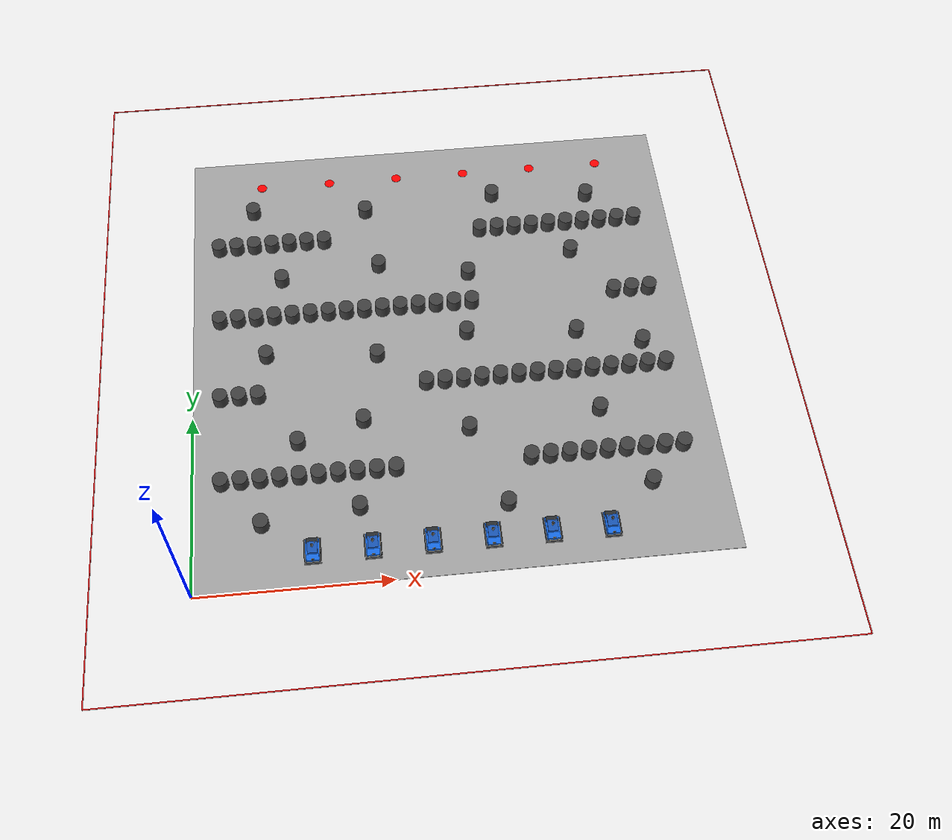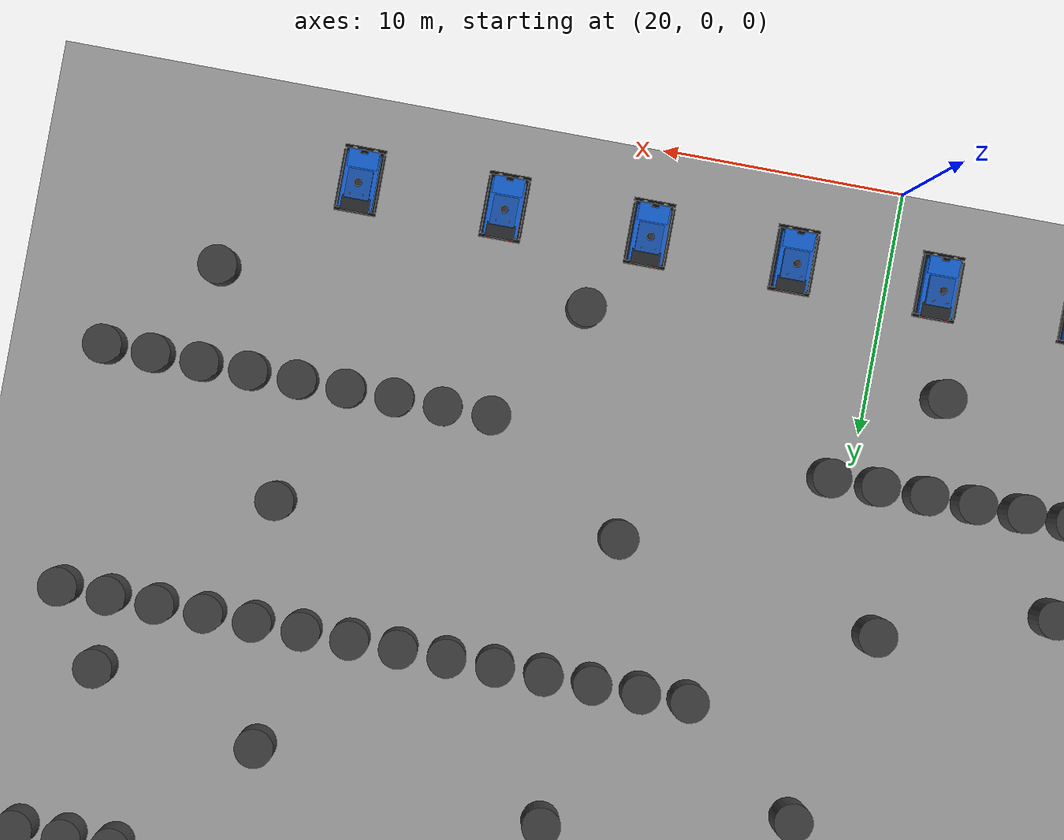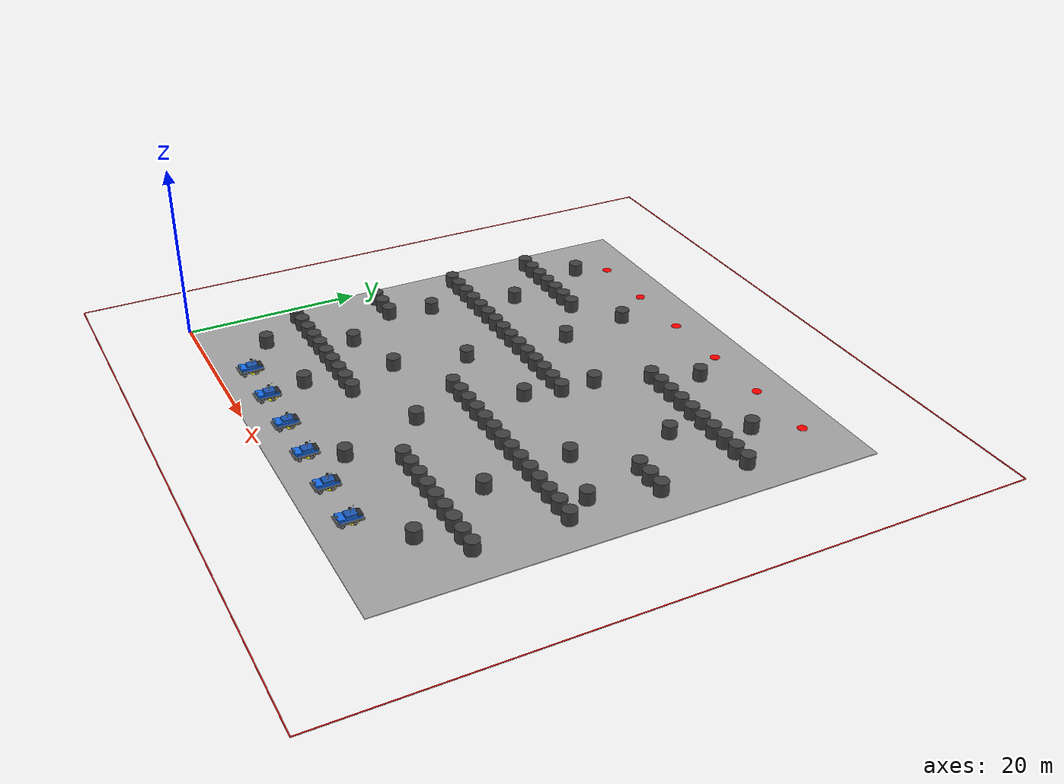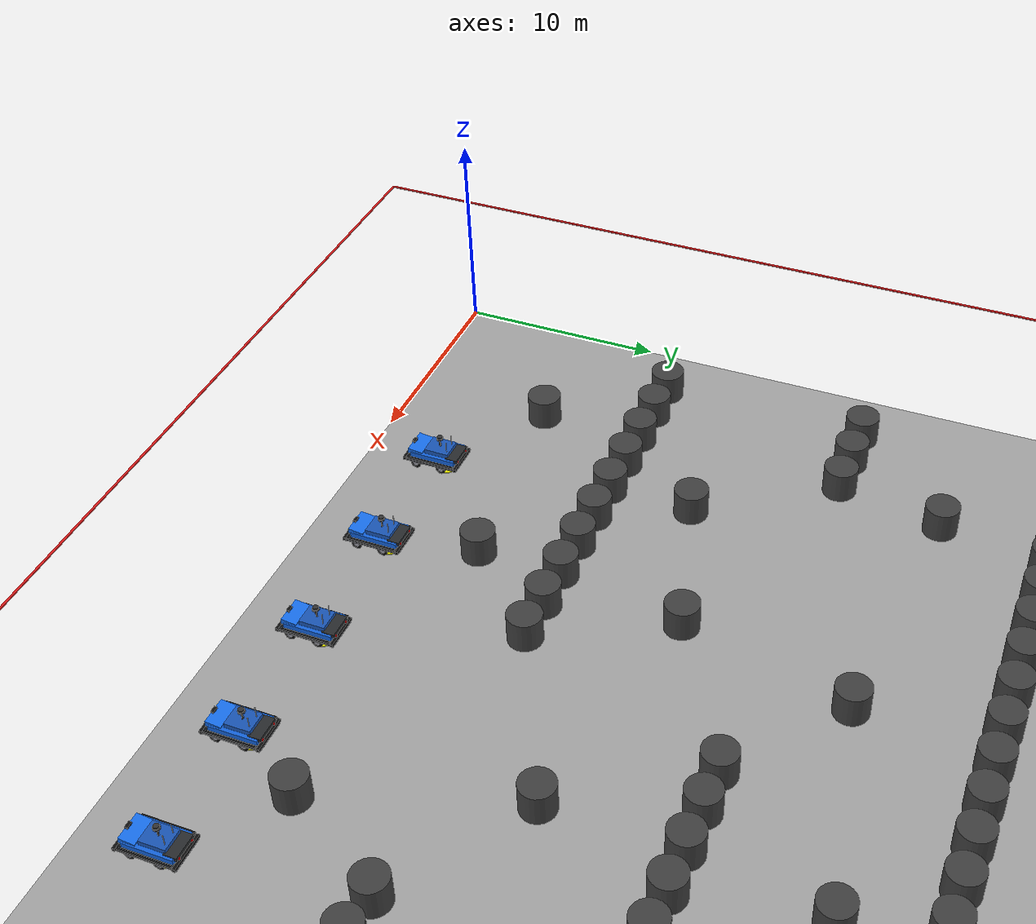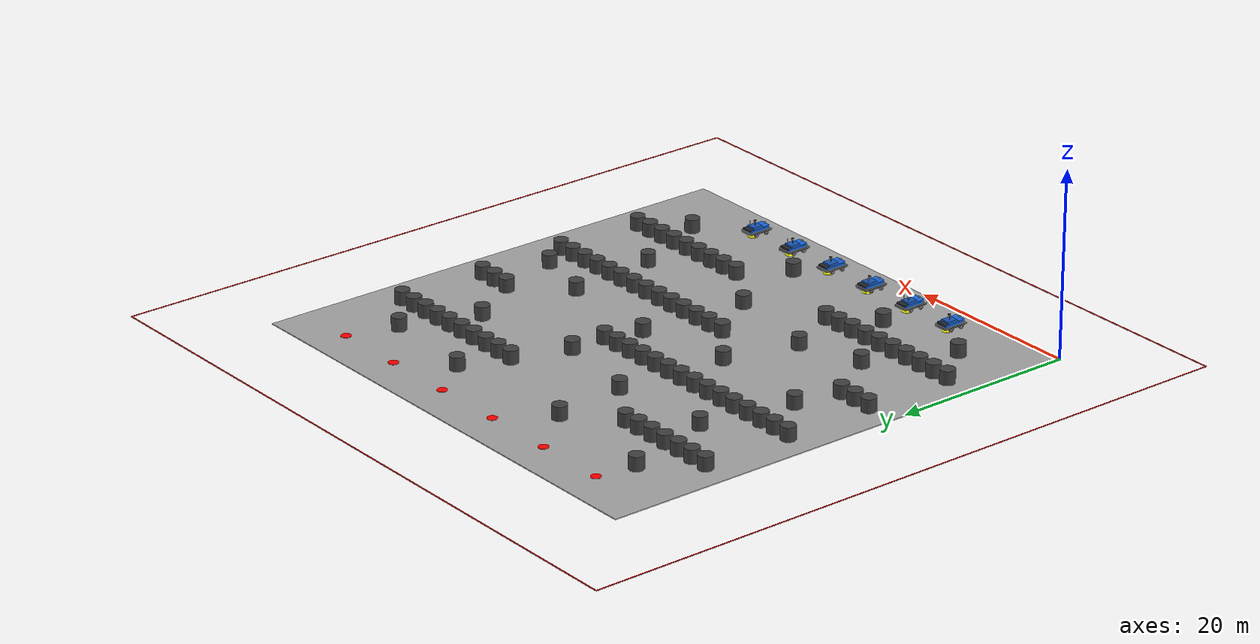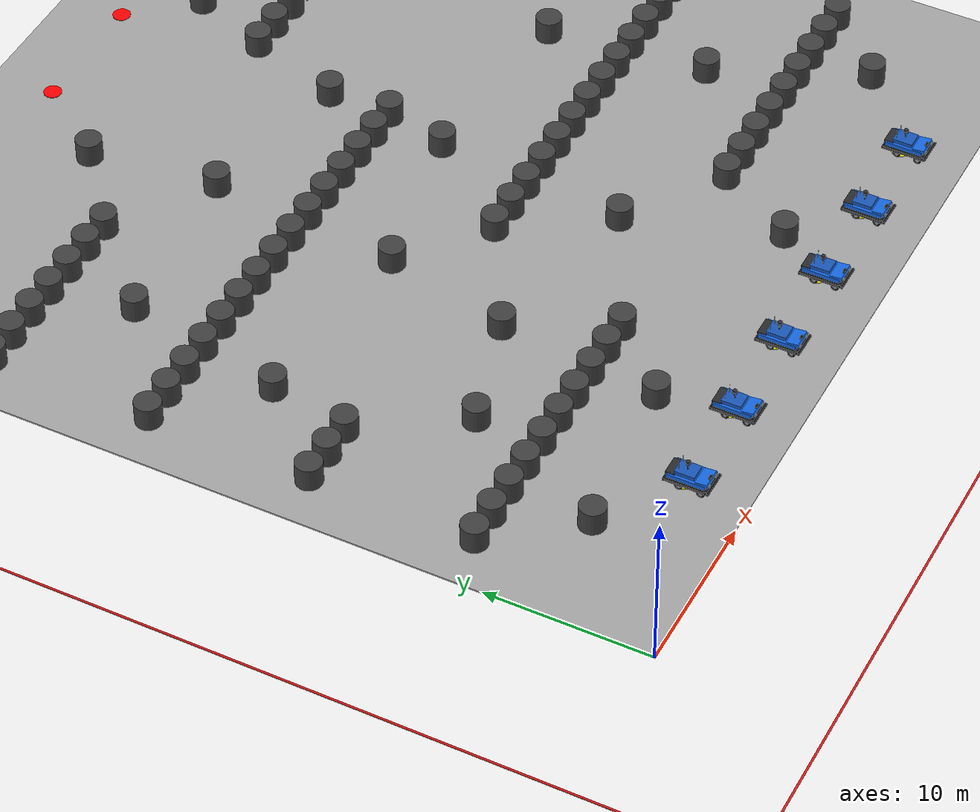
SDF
<?xml version="1.0"?>
<sdf version="1.10">

  <world name="paper_corridors_6ugv">

    <physics name="physics" type="ignored">
      <max_step_size>0.02</max_step_size>
      <real_time_factor>80.0</real_time_factor>
    </physics>

    <plugin
      filename="gz-sim-physics-system"
      name="gz::sim::systems::Physics"/>

    <plugin
      filename="gz-sim-user-commands-system"
      name="gz::sim::systems::UserCommands"/>

    <plugin
      filename="gz-sim-scene-broadcaster-system"
      name="gz::sim::systems::SceneBroadcaster"/>

    <light type="directional" name="sun">
      <cast_shadows>false</cast_shadows>
      <pose>27.5 27.5 60 0 0 0</pose>
      <diffuse>0.8 0.8 0.8 1</diffuse>
      <specular>0.2 0.2 0.2 1</specular>
      <direction>-0.4 0.2 -0.9</direction>
    </light>

    <model name="planner_workspace">
      <static>true</static>

      <pose>27.5 27.5 -0.05 0 0 0</pose>

      <link name="link">

        <collision name="collision">
          <geometry>
            <box>
              <size>75 75 0.10</size>
            </box>
          </geometry>
        </collision>

        <visual name="visual">
          <geometry>
            <box>
              <size>55 55 0.10</size>
            </box>
          </geometry>

          <material>
            <ambient>0.65 0.65 0.65 1.0</ambient>
            <diffuse>0.65 0.65 0.65 1.0</diffuse>
          </material>
        </visual>

      </link>
    </model>

    <model name="boundary_south">
      <static>true</static>
      <pose>27.5 -10.0 0.03 0 0 0</pose>

      <link name="link">
        <visual name="visual">
          <geometry>
            <box>
              <size>75.0 0.12 0.06</size>
            </box>
          </geometry>

          <material>
            <ambient>0.85 0.1 0.1 1.0</ambient>
            <diffuse>0.85 0.1 0.1 1.0</diffuse>
          </material>
        </visual>
      </link>
    </model>

    <model name="boundary_north">
      <static>true</static>
      <pose>27.5 65.0 0.03 0 0 0</pose>

      <link name="link">
        <visual name="visual">
          <geometry>
            <box>
              <size>75.0 0.12 0.06</size>
            </box>
          </geometry>

          <material>
            <ambient>0.85 0.1 0.1 1.0</ambient>
            <diffuse>0.85 0.1 0.1 1.0</diffuse>
          </material>
        </visual>
      </link>
    </model>

    <model name="boundary_west">
      <static>true</static>
      <pose>-10.0 27.5 0.03 0 0 0</pose>

      <link name="link">
        <visual name="visual">
          <geometry>
            <box>
              <size>0.12 75.0 0.06</size>
            </box>
          </geometry>

          <material>
            <ambient>0.85 0.1 0.1 1.0</ambient>
            <diffuse>0.85 0.1 0.1 1.0</diffuse>
          </material>
        </visual>
      </link>
    </model>

    <model name="boundary_east">
      <static>true</static>
      <pose>65.0 27.5 0.03 0 0 0</pose>

      <link name="link">
        <visual name="visual">
          <geometry>
            <box>
              <size>0.12 75.0 0.06</size>
            </box>
          </geometry>

          <material>
            <ambient>0.85 0.1 0.1 1.0</ambient>
            <diffuse>0.85 0.1 0.1 1.0</diffuse>
          </material>
        </visual>
      </link>
    </model>

    <model name="obstacle_000">
      <static>true</static>
      <pose>3.0 12.0 0.75 0 0 0</pose>

      <link name="link">

        <collision name="collision">
          <geometry>
            <cylinder>
              <radius>0.8</radius>
              <length>1.5</length>
            </cylinder>
          </geometry>
        </collision>

        <visual name="visual">
          <geometry>
            <cylinder>
              <radius>0.8</radius>
              <length>1.5</length>
            </cylinder>
          </geometry>

          <material>
            <ambient>0.25 0.25 0.25 1.0</ambient>
            <diffuse>0.25 0.25 0.25 1.0</diffuse>
          </material>
        </visual>

      </link>
    </model>

    <model name="obstacle_001">
      <static>true</static>
      <pose>5.0 12.0 0.75 0 0 0</pose>

      <link name="link">

        <collision name="collision">
          <geometry>
            <cylinder>
              <radius>0.8</radius>
              <length>1.5</length>
            </cylinder>
          </geometry>
        </collision>

        <visual name="visual">
          <geometry>
            <cylinder>
              <radius>0.8</radius>
              <length>1.5</length>
            </cylinder>
          </geometry>

          <material>
            <ambient>0.25 0.25 0.25 1.0</ambient>
            <diffuse>0.25 0.25 0.25 1.0</diffuse>
          </material>
        </visual>

      </link>
    </model>

    <model name="obstacle_002">
      <static>true</static>
      <pose>7.0 12.0 0.75 0 0 0</pose>

      <link name="link">

        <collision name="collision">
          <geometry>
            <cylinder>
              <radius>0.8</radius>
              <length>1.5</length>
            </cylinder>
          </geometry>
        </collision>

        <visual name="visual">
          <geometry>
            <cylinder>
              <radius>0.8</radius>
              <length>1.5</length>
            </cylinder>
          </geometry>

          <material>
            <ambient>0.25 0.25 0.25 1.0</ambient>
            <diffuse>0.25 0.25 0.25 1.0</diffuse>
          </material>
        </visual>

      </link>
    </model>

    <model name="obstacle_003">
      <static>true</static>
      <pose>9.0 12.0 0.75 0 0 0</pose>

      <link name="link">

        <collision name="collision">
          <geometry>
            <cylinder>
              <radius>0.8</radius>
              <length>1.5</length>
            </cylinder>
          </geometry>
        </collision>

        <visual name="visual">
          <geometry>
            <cylinder>
              <radius>0.8</radius>
              <length>1.5</length>
            </cylinder>
          </geometry>

          <material>
            <ambient>0.25 0.25 0.25 1.0</ambient>
            <diffuse>0.25 0.25 0.25 1.0</diffuse>
          </material>
        </visual>

      </link>
    </model>

    <model name="obstacle_004">
      <static>true</static>
      <pose>11.0 12.0 0.75 0 0 0</pose>

      <link name="link">

        <collision name="collision">
          <geometry>
            <cylinder>
              <radius>0.8</radius>
              <length>1.5</length>
            </cylinder>
          </geometry>
        </collision>

        <visual name="visual">
          <geometry>
            <cylinder>
              <radius>0.8</radius>
              <length>1.5</length>
            </cylinder>
          </geometry>

          <material>
            <ambient>0.25 0.25 0.25 1.0</ambient>
            <diffuse>0.25 0.25 0.25 1.0</diffuse>
          </material>
        </visual>

      </link>
    </model>

    <model name="obstacle_005">
      <static>true</static>
      <pose>13.0 12.0 0.75 0 0 0</pose>

      <link name="link">

        <collision name="collision">
          <geometry>
            <cylinder>
              <radius>0.8</radius>
              <length>1.5</length>
            </cylinder>
          </geometry>
        </collision>

        <visual name="visual">
          <geometry>
            <cylinder>
              <radius>0.8</radius>
              <length>1.5</length>
            </cylinder>
          </geometry>

          <material>
            <ambient>0.25 0.25 0.25 1.0</ambient>
            <diffuse>0.25 0.25 0.25 1.0</diffuse>
          </material>
        </visual>

      </link>
    </model>

    <model name="obstacle_006">
      <static>true</static>
      <pose>15.0 12.0 0.75 0 0 0</pose>

      <link name="link">

        <collision name="collision">
          <geometry>
            <cylinder>
              <radius>0.8</radius>
              <length>1.5</length>
            </cylinder>
          </geometry>
        </collision>

        <visual name="visual">
          <geometry>
            <cylinder>
              <radius>0.8</radius>
              <length>1.5</length>
            </cylinder>
          </geometry>

          <material>
            <ambient>0.25 0.25 0.25 1.0</ambient>
            <diffuse>0.25 0.25 0.25 1.0</diffuse>
          </material>
        </visual>

      </link>
    </model>

    <model name="obstacle_007">
      <static>true</static>
      <pose>17.0 12.0 0.75 0 0 0</pose>

      <link name="link">

        <collision name="collision">
          <geometry>
            <cylinder>
              <radius>0.8</radius>
              <length>1.5</length>
            </cylinder>
          </geometry>
        </collision>

        <visual name="visual">
          <geometry>
            <cylinder>
              <radius>0.8</radius>
              <length>1.5</length>
            </cylinder>
          </geometry>

          <material>
            <ambient>0.25 0.25 0.25 1.0</ambient>
            <diffuse>0.25 0.25 0.25 1.0</diffuse>
          </material>
        </visual>

      </link>
    </model>

    <model name="obstacle_008">
      <static>true</static>
      <pose>19.0 12.0 0.75 0 0 0</pose>

      <link name="link">

        <collision name="collision">
          <geometry>
            <cylinder>
              <radius>0.8</radius>
              <length>1.5</length>
            </cylinder>
          </geometry>
        </collision>

        <visual name="visual">
          <geometry>
            <cylinder>
              <radius>0.8</radius>
              <length>1.5</length>
            </cylinder>
          </geometry>

          <material>
            <ambient>0.25 0.25 0.25 1.0</ambient>
            <diffuse>0.25 0.25 0.25 1.0</diffuse>
          </material>
        </visual>

      </link>
    </model>

    <model name="obstacle_009">
      <static>true</static>
      <pose>21.0 12.0 0.75 0 0 0</pose>

      <link name="link">

        <collision name="collision">
          <geometry>
            <cylinder>
              <radius>0.8</radius>
              <length>1.5</length>
            </cylinder>
          </geometry>
        </collision>

        <visual name="visual">
          <geometry>
            <cylinder>
              <radius>0.8</radius>
              <length>1.5</length>
            </cylinder>
          </geometry>

          <material>
            <ambient>0.25 0.25 0.25 1.0</ambient>
            <diffuse>0.25 0.25 0.25 1.0</diffuse>
          </material>
        </visual>

      </link>
    </model>

    <model name="obstacle_010">
      <static>true</static>
      <pose>35.0 12.0 0.75 0 0 0</pose>

      <link name="link">

        <collision name="collision">
          <geometry>
            <cylinder>
              <radius>0.8</radius>
              <length>1.5</length>
            </cylinder>
          </geometry>
        </collision>

        <visual name="visual">
          <geometry>
            <cylinder>
              <radius>0.8</radius>
              <length>1.5</length>
            </cylinder>
          </geometry>

          <material>
            <ambient>0.25 0.25 0.25 1.0</ambient>
            <diffuse>0.25 0.25 0.25 1.0</diffuse>
          </material>
        </visual>

      </link>
    </model>

    <model name="obstacle_011">
      <static>true</static>
      <pose>37.0 12.0 0.75 0 0 0</pose>

      <link name="link">

        <collision name="collision">
          <geometry>
            <cylinder>
              <radius>0.8</radius>
              <length>1.5</length>
            </cylinder>
          </geometry>
        </collision>

        <visual name="visual">
          <geometry>
            <cylinder>
              <radius>0.8</radius>
              <length>1.5</length>
            </cylinder>
          </geometry>

          <material>
            <ambient>0.25 0.25 0.25 1.0</ambient>
            <diffuse>0.25 0.25 0.25 1.0</diffuse>
          </material>
        </visual>

      </link>
    </model>

    <model name="obstacle_012">
      <static>true</static>
      <pose>39.0 12.0 0.75 0 0 0</pose>

      <link name="link">

        <collision name="collision">
          <geometry>
            <cylinder>
              <radius>0.8</radius>
              <length>1.5</length>
            </cylinder>
          </geometry>
        </collision>

        <visual name="visual">
          <geometry>
            <cylinder>
              <radius>0.8</radius>
              <length>1.5</length>
            </cylinder>
          </geometry>

          <material>
            <ambient>0.25 0.25 0.25 1.0</ambient>
            <diffuse>0.25 0.25 0.25 1.0</diffuse>
          </material>
        </visual>

      </link>
    </model>

    <model name="obstacle_013">
      <static>true</static>
      <pose>41.0 12.0 0.75 0 0 0</pose>

      <link name="link">

        <collision name="collision">
          <geometry>
            <cylinder>
              <radius>0.8</radius>
              <length>1.5</length>
            </cylinder>
          </geometry>
        </collision>

        <visual name="visual">
          <geometry>
            <cylinder>
              <radius>0.8</radius>
              <length>1.5</length>
            </cylinder>
          </geometry>

          <material>
            <ambient>0.25 0.25 0.25 1.0</ambient>
            <diffuse>0.25 0.25 0.25 1.0</diffuse>
          </material>
        </visual>

      </link>
    </model>

    <model name="obstacle_014">
      <static>true</static>
      <pose>43.0 12.0 0.75 0 0 0</pose>

      <link name="link">

        <collision name="collision">
          <geometry>
            <cylinder>
              <radius>0.8</radius>
              <length>1.5</length>
            </cylinder>
          </geometry>
        </collision>

        <visual name="visual">
          <geometry>
            <cylinder>
              <radius>0.8</radius>
              <length>1.5</length>
            </cylinder>
          </geometry>

          <material>
            <ambient>0.25 0.25 0.25 1.0</ambient>
            <diffuse>0.25 0.25 0.25 1.0</diffuse>
          </material>
        </visual>

      </link>
    </model>

    <model name="obstacle_015">
      <static>true</static>
      <pose>45.0 12.0 0.75 0 0 0</pose>

      <link name="link">

        <collision name="collision">
          <geometry>
            <cylinder>
              <radius>0.8</radius>
              <length>1.5</length>
            </cylinder>
          </geometry>
        </collision>

        <visual name="visual">
          <geometry>
            <cylinder>
              <radius>0.8</radius>
              <length>1.5</length>
            </cylinder>
          </geometry>

          <material>
            <ambient>0.25 0.25 0.25 1.0</ambient>
            <diffuse>0.25 0.25 0.25 1.0</diffuse>
          </material>
        </visual>

      </link>
    </model>

    <model name="obstacle_016">
      <static>true</static>
      <pose>47.0 12.0 0.75 0 0 0</pose>

      <link name="link">

        <collision name="collision">
          <geometry>
            <cylinder>
              <radius>0.8</radius>
              <length>1.5</length>
            </cylinder>
          </geometry>
        </collision>

        <visual name="visual">
          <geometry>
            <cylinder>
              <radius>0.8</radius>
              <length>1.5</length>
            </cylinder>
          </geometry>

          <material>
            <ambient>0.25 0.25 0.25 1.0</ambient>
            <diffuse>0.25 0.25 0.25 1.0</diffuse>
          </material>
        </visual>

      </link>
    </model>

    <model name="obstacle_017">
      <static>true</static>
      <pose>49.0 12.0 0.75 0 0 0</pose>

      <link name="link">

        <collision name="collision">
          <geometry>
            <cylinder>
              <radius>0.8</radius>
              <length>1.5</length>
            </cylinder>
          </geometry>
        </collision>

        <visual name="visual">
          <geometry>
            <cylinder>
              <radius>0.8</radius>
              <length>1.5</length>
            </cylinder>
          </geometry>

          <material>
            <ambient>0.25 0.25 0.25 1.0</ambient>
            <diffuse>0.25 0.25 0.25 1.0</diffuse>
          </material>
        </visual>

      </link>
    </model>

    <model name="obstacle_018">
      <static>true</static>
      <pose>51.0 12.0 0.75 0 0 0</pose>

      <link name="link">

        <collision name="collision">
          <geometry>
            <cylinder>
              <radius>0.8</radius>
              <length>1.5</length>
            </cylinder>
          </geometry>
        </collision>

        <visual name="visual">
          <geometry>
            <cylinder>
              <radius>0.8</radius>
              <length>1.5</length>
            </cylinder>
          </geometry>

          <material>
            <ambient>0.25 0.25 0.25 1.0</ambient>
            <diffuse>0.25 0.25 0.25 1.0</diffuse>
          </material>
        </visual>

      </link>
    </model>

    <model name="obstacle_019">
      <static>true</static>
      <pose>3.0 22.0 0.75 0 0 0</pose>

      <link name="link">

        <collision name="collision">
          <geometry>
            <cylinder>
              <radius>0.8</radius>
              <length>1.5</length>
            </cylinder>
          </geometry>
        </collision>

        <visual name="visual">
          <geometry>
            <cylinder>
              <radius>0.8</radius>
              <length>1.5</length>
            </cylinder>
          </geometry>

          <material>
            <ambient>0.25 0.25 0.25 1.0</ambient>
            <diffuse>0.25 0.25 0.25 1.0</diffuse>
          </material>
        </visual>

      </link>
    </model>

    <model name="obstacle_020">
      <static>true</static>
      <pose>5.0 22.0 0.75 0 0 0</pose>

      <link name="link">

        <collision name="collision">
          <geometry>
            <cylinder>
              <radius>0.8</radius>
              <length>1.5</length>
            </cylinder>
          </geometry>
        </collision>

        <visual name="visual">
          <geometry>
            <cylinder>
              <radius>0.8</radius>
              <length>1.5</length>
            </cylinder>
          </geometry>

          <material>
            <ambient>0.25 0.25 0.25 1.0</ambient>
            <diffuse>0.25 0.25 0.25 1.0</diffuse>
          </material>
        </visual>

      </link>
    </model>

    <model name="obstacle_021">
      <static>true</static>
      <pose>7.0 22.0 0.75 0 0 0</pose>

      <link name="link">

        <collision name="collision">
          <geometry>
            <cylinder>
              <radius>0.8</radius>
              <length>1.5</length>
            </cylinder>
          </geometry>
        </collision>

        <visual name="visual">
          <geometry>
            <cylinder>
              <radius>0.8</radius>
              <length>1.5</length>
            </cylinder>
          </geometry>

          <material>
            <ambient>0.25 0.25 0.25 1.0</ambient>
            <diffuse>0.25 0.25 0.25 1.0</diffuse>
          </material>
        </visual>

      </link>
    </model>

    <model name="obstacle_022">
      <static>true</static>
      <pose>25.0 22.0 0.75 0 0 0</pose>

      <link name="link">

        <collision name="collision">
          <geometry>
            <cylinder>
              <radius>0.8</radius>
              <length>1.5</length>
            </cylinder>
          </geometry>
        </collision>

        <visual name="visual">
          <geometry>
            <cylinder>
              <radius>0.8</radius>
              <length>1.5</length>
            </cylinder>
          </geometry>

          <material>
            <ambient>0.25 0.25 0.25 1.0</ambient>
            <diffuse>0.25 0.25 0.25 1.0</diffuse>
          </material>
        </visual>

      </link>
    </model>

    <model name="obstacle_023">
      <static>true</static>
      <pose>27.0 22.0 0.75 0 0 0</pose>

      <link name="link">

        <collision name="collision">
          <geometry>
            <cylinder>
              <radius>0.8</radius>
              <length>1.5</length>
            </cylinder>
          </geometry>
        </collision>

        <visual name="visual">
          <geometry>
            <cylinder>
              <radius>0.8</radius>
              <length>1.5</length>
            </cylinder>
          </geometry>

          <material>
            <ambient>0.25 0.25 0.25 1.0</ambient>
            <diffuse>0.25 0.25 0.25 1.0</diffuse>
          </material>
        </visual>

      </link>
    </model>

    <model name="obstacle_024">
      <static>true</static>
      <pose>29.0 22.0 0.75 0 0 0</pose>

      <link name="link">

        <collision name="collision">
          <geometry>
            <cylinder>
              <radius>0.8</radius>
              <length>1.5</length>
            </cylinder>
          </geometry>
        </collision>

        <visual name="visual">
          <geometry>
            <cylinder>
              <radius>0.8</radius>
              <length>1.5</length>
            </cylinder>
          </geometry>

          <material>
            <ambient>0.25 0.25 0.25 1.0</ambient>
            <diffuse>0.25 0.25 0.25 1.0</diffuse>
          </material>
        </visual>

      </link>
    </model>

    <model name="obstacle_025">
      <static>true</static>
      <pose>31.0 22.0 0.75 0 0 0</pose>

      <link name="link">

        <collision name="collision">
          <geometry>
            <cylinder>
              <radius>0.8</radius>
              <length>1.5</length>
            </cylinder>
          </geometry>
        </collision>

        <visual name="visual">
          <geometry>
            <cylinder>
              <radius>0.8</radius>
              <length>1.5</length>
            </cylinder>
          </geometry>

          <material>
            <ambient>0.25 0.25 0.25 1.0</ambient>
            <diffuse>0.25 0.25 0.25 1.0</diffuse>
          </material>
        </visual>

      </link>
    </model>

    <model name="obstacle_026">
      <static>true</static>
      <pose>33.0 22.0 0.75 0 0 0</pose>

      <link name="link">

        <collision name="collision">
          <geometry>
            <cylinder>
              <radius>0.8</radius>
              <length>1.5</length>
            </cylinder>
          </geometry>
        </collision>

        <visual name="visual">
          <geometry>
            <cylinder>
              <radius>0.8</radius>
              <length>1.5</length>
            </cylinder>
          </geometry>

          <material>
            <ambient>0.25 0.25 0.25 1.0</ambient>
            <diffuse>0.25 0.25 0.25 1.0</diffuse>
          </material>
        </visual>

      </link>
    </model>

    <model name="obstacle_027">
      <static>true</static>
      <pose>35.0 22.0 0.75 0 0 0</pose>

      <link name="link">

        <collision name="collision">
          <geometry>
            <cylinder>
              <radius>0.8</radius>
              <length>1.5</length>
            </cylinder>
          </geometry>
        </collision>

        <visual name="visual">
          <geometry>
            <cylinder>
              <radius>0.8</radius>
              <length>1.5</length>
            </cylinder>
          </geometry>

          <material>
            <ambient>0.25 0.25 0.25 1.0</ambient>
            <diffuse>0.25 0.25 0.25 1.0</diffuse>
          </material>
        </visual>

      </link>
    </model>

    <model name="obstacle_028">
      <static>true</static>
      <pose>37.0 22.0 0.75 0 0 0</pose>

      <link name="link">

        <collision name="collision">
          <geometry>
            <cylinder>
              <radius>0.8</radius>
              <length>1.5</length>
            </cylinder>
          </geometry>
        </collision>

        <visual name="visual">
          <geometry>
            <cylinder>
              <radius>0.8</radius>
              <length>1.5</length>
            </cylinder>
          </geometry>

          <material>
            <ambient>0.25 0.25 0.25 1.0</ambient>
            <diffuse>0.25 0.25 0.25 1.0</diffuse>
          </material>
        </visual>

      </link>
    </model>

    <model name="obstacle_029">
      <static>true</static>
      <pose>39.0 22.0 0.75 0 0 0</pose>

      <link name="link">

        <collision name="collision">
          <geometry>
            <cylinder>
              <radius>0.8</radius>
              <length>1.5</length>
            </cylinder>
          </geometry>
        </collision>

        <visual name="visual">
          <geometry>
            <cylinder>
              <radius>0.8</radius>
              <length>1.5</length>
            </cylinder>
          </geometry>

          <material>
            <ambient>0.25 0.25 0.25 1.0</ambient>
            <diffuse>0.25 0.25 0.25 1.0</diffuse>
          </material>
        </visual>

      </link>
    </model>

    <model name="obstacle_030">
      <static>true</static>
      <pose>41.0 22.0 0.75 0 0 0</pose>

      <link name="link">

        <collision name="collision">
          <geometry>
            <cylinder>
              <radius>0.8</radius>
              <length>1.5</length>
            </cylinder>
          </geometry>
        </collision>

        <visual name="visual">
          <geometry>
            <cylinder>
              <radius>0.8</radius>
              <length>1.5</length>
            </cylinder>
          </geometry>

          <material>
            <ambient>0.25 0.25 0.25 1.0</ambient>
            <diffuse>0.25 0.25 0.25 1.0</diffuse>
          </material>
        </visual>

      </link>
    </model>

    <model name="obstacle_031">
      <static>true</static>
      <pose>43.0 22.0 0.75 0 0 0</pose>

      <link name="link">

        <collision name="collision">
          <geometry>
            <cylinder>
              <radius>0.8</radius>
              <length>1.5</length>
            </cylinder>
          </geometry>
        </collision>

        <visual name="visual">
          <geometry>
            <cylinder>
              <radius>0.8</radius>
              <length>1.5</length>
            </cylinder>
          </geometry>

          <material>
            <ambient>0.25 0.25 0.25 1.0</ambient>
            <diffuse>0.25 0.25 0.25 1.0</diffuse>
          </material>
        </visual>

      </link>
    </model>

    <model name="obstacle_032">
      <static>true</static>
      <pose>45.0 22.0 0.75 0 0 0</pose>

      <link name="link">

        <collision name="collision">
          <geometry>
            <cylinder>
              <radius>0.8</radius>
              <length>1.5</length>
            </cylinder>
          </geometry>
        </collision>

        <visual name="visual">
          <geometry>
            <cylinder>
              <radius>0.8</radius>
              <length>1.5</length>
            </cylinder>
          </geometry>

          <material>
            <ambient>0.25 0.25 0.25 1.0</ambient>
            <diffuse>0.25 0.25 0.25 1.0</diffuse>
          </material>
        </visual>

      </link>
    </model>

    <model name="obstacle_033">
      <static>true</static>
      <pose>47.0 22.0 0.75 0 0 0</pose>

      <link name="link">

        <collision name="collision">
          <geometry>
            <cylinder>
              <radius>0.8</radius>
              <length>1.5</length>
            </cylinder>
          </geometry>
        </collision>

        <visual name="visual">
          <geometry>
            <cylinder>
              <radius>0.8</radius>
              <length>1.5</length>
            </cylinder>
          </geometry>

          <material>
            <ambient>0.25 0.25 0.25 1.0</ambient>
            <diffuse>0.25 0.25 0.25 1.0</diffuse>
          </material>
        </visual>

      </link>
    </model>

    <model name="obstacle_034">
      <static>true</static>
      <pose>49.0 22.0 0.75 0 0 0</pose>

      <link name="link">

        <collision name="collision">
          <geometry>
            <cylinder>
              <radius>0.8</radius>
              <length>1.5</length>
            </cylinder>
          </geometry>
        </collision>

        <visual name="visual">
          <geometry>
            <cylinder>
              <radius>0.8</radius>
              <length>1.5</length>
            </cylinder>
          </geometry>

          <material>
            <ambient>0.25 0.25 0.25 1.0</ambient>
            <diffuse>0.25 0.25 0.25 1.0</diffuse>
          </material>
        </visual>

      </link>
    </model>

    <model name="obstacle_035">
      <static>true</static>
      <pose>51.0 22.0 0.75 0 0 0</pose>

      <link name="link">

        <collision name="collision">
          <geometry>
            <cylinder>
              <radius>0.8</radius>
              <length>1.5</length>
            </cylinder>
          </geometry>
        </collision>

        <visual name="visual">
          <geometry>
            <cylinder>
              <radius>0.8</radius>
              <length>1.5</length>
            </cylinder>
          </geometry>

          <material>
            <ambient>0.25 0.25 0.25 1.0</ambient>
            <diffuse>0.25 0.25 0.25 1.0</diffuse>
          </material>
        </visual>

      </link>
    </model>

    <model name="obstacle_036">
      <static>true</static>
      <pose>3.0 32.0 0.75 0 0 0</pose>

      <link name="link">

        <collision name="collision">
          <geometry>
            <cylinder>
              <radius>0.8</radius>
              <length>1.5</length>
            </cylinder>
          </geometry>
        </collision>

        <visual name="visual">
          <geometry>
            <cylinder>
              <radius>0.8</radius>
              <length>1.5</length>
            </cylinder>
          </geometry>

          <material>
            <ambient>0.25 0.25 0.25 1.0</ambient>
            <diffuse>0.25 0.25 0.25 1.0</diffuse>
          </material>
        </visual>

      </link>
    </model>

    <model name="obstacle_037">
      <static>true</static>
      <pose>5.0 32.0 0.75 0 0 0</pose>

      <link name="link">

        <collision name="collision">
          <geometry>
            <cylinder>
              <radius>0.8</radius>
              <length>1.5</length>
            </cylinder>
          </geometry>
        </collision>

        <visual name="visual">
          <geometry>
            <cylinder>
              <radius>0.8</radius>
              <length>1.5</length>
            </cylinder>
          </geometry>

          <material>
            <ambient>0.25 0.25 0.25 1.0</ambient>
            <diffuse>0.25 0.25 0.25 1.0</diffuse>
          </material>
        </visual>

      </link>
    </model>

    <model name="obstacle_038">
      <static>true</static>
      <pose>7.0 32.0 0.75 0 0 0</pose>

      <link name="link">

        <collision name="collision">
          <geometry>
            <cylinder>
              <radius>0.8</radius>
              <length>1.5</length>
            </cylinder>
          </geometry>
        </collision>

        <visual name="visual">
          <geometry>
            <cylinder>
              <radius>0.8</radius>
              <length>1.5</length>
            </cylinder>
          </geometry>

          <material>
            <ambient>0.25 0.25 0.25 1.0</ambient>
            <diffuse>0.25 0.25 0.25 1.0</diffuse>
          </material>
        </visual>

      </link>
    </model>

    <model name="obstacle_039">
      <static>true</static>
      <pose>9.0 32.0 0.75 0 0 0</pose>

      <link name="link">

        <collision name="collision">
          <geometry>
            <cylinder>
              <radius>0.8</radius>
              <length>1.5</length>
            </cylinder>
          </geometry>
        </collision>

        <visual name="visual">
          <geometry>
            <cylinder>
              <radius>0.8</radius>
              <length>1.5</length>
            </cylinder>
          </geometry>

          <material>
            <ambient>0.25 0.25 0.25 1.0</ambient>
            <diffuse>0.25 0.25 0.25 1.0</diffuse>
          </material>
        </visual>

      </link>
    </model>

    <model name="obstacle_040">
      <static>true</static>
      <pose>11.0 32.0 0.75 0 0 0</pose>

      <link name="link">

        <collision name="collision">
          <geometry>
            <cylinder>
              <radius>0.8</radius>
              <length>1.5</length>
            </cylinder>
          </geometry>
        </collision>

        <visual name="visual">
          <geometry>
            <cylinder>
              <radius>0.8</radius>
              <length>1.5</length>
            </cylinder>
          </geometry>

          <material>
            <ambient>0.25 0.25 0.25 1.0</ambient>
            <diffuse>0.25 0.25 0.25 1.0</diffuse>
          </material>
        </visual>

      </link>
    </model>

    <model name="obstacle_041">
      <static>true</static>
      <pose>13.0 32.0 0.75 0 0 0</pose>

      <link name="link">

        <collision name="collision">
          <geometry>
            <cylinder>
              <radius>0.8</radius>
              <length>1.5</length>
            </cylinder>
          </geometry>
        </collision>

        <visual name="visual">
          <geometry>
            <cylinder>
              <radius>0.8</radius>
              <length>1.5</length>
            </cylinder>
          </geometry>

          <material>
            <ambient>0.25 0.25 0.25 1.0</ambient>
            <diffuse>0.25 0.25 0.25 1.0</diffuse>
          </material>
        </visual>

      </link>
    </model>

    <model name="obstacle_042">
      <static>true</static>
      <pose>15.0 32.0 0.75 0 0 0</pose>

      <link name="link">

        <collision name="collision">
          <geometry>
            <cylinder>
              <radius>0.8</radius>
              <length>1.5</length>
            </cylinder>
          </geometry>
        </collision>

        <visual name="visual">
          <geometry>
            <cylinder>
              <radius>0.8</radius>
              <length>1.5</length>
            </cylinder>
          </geometry>

          <material>
            <ambient>0.25 0.25 0.25 1.0</ambient>
            <diffuse>0.25 0.25 0.25 1.0</diffuse>
          </material>
        </visual>

      </link>
    </model>

    <model name="obstacle_043">
      <static>true</static>
      <pose>17.0 32.0 0.75 0 0 0</pose>

      <link name="link">

        <collision name="collision">
          <geometry>
            <cylinder>
              <radius>0.8</radius>
              <length>1.5</length>
            </cylinder>
          </geometry>
        </collision>

        <visual name="visual">
          <geometry>
            <cylinder>
              <radius>0.8</radius>
              <length>1.5</length>
            </cylinder>
          </geometry>

          <material>
            <ambient>0.25 0.25 0.25 1.0</ambient>
            <diffuse>0.25 0.25 0.25 1.0</diffuse>
          </material>
        </visual>

      </link>
    </model>

    <model name="obstacle_044">
      <static>true</static>
      <pose>19.0 32.0 0.75 0 0 0</pose>

      <link name="link">

        <collision name="collision">
          <geometry>
            <cylinder>
              <radius>0.8</radius>
              <length>1.5</length>
            </cylinder>
          </geometry>
        </collision>

        <visual name="visual">
          <geometry>
            <cylinder>
              <radius>0.8</radius>
              <length>1.5</length>
            </cylinder>
          </geometry>

          <material>
            <ambient>0.25 0.25 0.25 1.0</ambient>
            <diffuse>0.25 0.25 0.25 1.0</diffuse>
          </material>
        </visual>

      </link>
    </model>

    <model name="obstacle_045">
      <static>true</static>
      <pose>21.0 32.0 0.75 0 0 0</pose>

      <link name="link">

        <collision name="collision">
          <geometry>
            <cylinder>
              <radius>0.8</radius>
              <length>1.5</length>
            </cylinder>
          </geometry>
        </collision>

        <visual name="visual">
          <geometry>
            <cylinder>
              <radius>0.8</radius>
              <length>1.5</length>
            </cylinder>
          </geometry>

          <material>
            <ambient>0.25 0.25 0.25 1.0</ambient>
            <diffuse>0.25 0.25 0.25 1.0</diffuse>
          </material>
        </visual>

      </link>
    </model>

    <model name="obstacle_046">
      <static>true</static>
      <pose>23.0 32.0 0.75 0 0 0</pose>

      <link name="link">

        <collision name="collision">
          <geometry>
            <cylinder>
              <radius>0.8</radius>
              <length>1.5</length>
            </cylinder>
          </geometry>
        </collision>

        <visual name="visual">
          <geometry>
            <cylinder>
              <radius>0.8</radius>
              <length>1.5</length>
            </cylinder>
          </geometry>

          <material>
            <ambient>0.25 0.25 0.25 1.0</ambient>
            <diffuse>0.25 0.25 0.25 1.0</diffuse>
          </material>
        </visual>

      </link>
    </model>

    <model name="obstacle_047">
      <static>true</static>
      <pose>25.0 32.0 0.75 0 0 0</pose>

      <link name="link">

        <collision name="collision">
          <geometry>
            <cylinder>
              <radius>0.8</radius>
              <length>1.5</length>
            </cylinder>
          </geometry>
        </collision>

        <visual name="visual">
          <geometry>
            <cylinder>
              <radius>0.8</radius>
              <length>1.5</length>
            </cylinder>
          </geometry>

          <material>
            <ambient>0.25 0.25 0.25 1.0</ambient>
            <diffuse>0.25 0.25 0.25 1.0</diffuse>
          </material>
        </visual>

      </link>
    </model>

    <model name="obstacle_048">
      <static>true</static>
      <pose>27.0 32.0 0.75 0 0 0</pose>

      <link name="link">

        <collision name="collision">
          <geometry>
            <cylinder>
              <radius>0.8</radius>
              <length>1.5</length>
            </cylinder>
          </geometry>
        </collision>

        <visual name="visual">
          <geometry>
            <cylinder>
              <radius>0.8</radius>
              <length>1.5</length>
            </cylinder>
          </geometry>

          <material>
            <ambient>0.25 0.25 0.25 1.0</ambient>
            <diffuse>0.25 0.25 0.25 1.0</diffuse>
          </material>
        </visual>

      </link>
    </model>

    <model name="obstacle_049">
      <static>true</static>
      <pose>29.0 32.0 0.75 0 0 0</pose>

      <link name="link">

        <collision name="collision">
          <geometry>
            <cylinder>
              <radius>0.8</radius>
              <length>1.5</length>
            </cylinder>
          </geometry>
        </collision>

        <visual name="visual">
          <geometry>
            <cylinder>
              <radius>0.8</radius>
              <length>1.5</length>
            </cylinder>
          </geometry>

          <material>
            <ambient>0.25 0.25 0.25 1.0</ambient>
            <diffuse>0.25 0.25 0.25 1.0</diffuse>
          </material>
        </visual>

      </link>
    </model>

    <model name="obstacle_050">
      <static>true</static>
      <pose>31.0 32.0 0.75 0 0 0</pose>

      <link name="link">

        <collision name="collision">
          <geometry>
            <cylinder>
              <radius>0.8</radius>
              <length>1.5</length>
            </cylinder>
          </geometry>
        </collision>

        <visual name="visual">
          <geometry>
            <cylinder>
              <radius>0.8</radius>
              <length>1.5</length>
            </cylinder>
          </geometry>

          <material>
            <ambient>0.25 0.25 0.25 1.0</ambient>
            <diffuse>0.25 0.25 0.25 1.0</diffuse>
          </material>
        </visual>

      </link>
    </model>

    <model name="obstacle_051">
      <static>true</static>
      <pose>47.0 32.0 0.75 0 0 0</pose>

      <link name="link">

        <collision name="collision">
          <geometry>
            <cylinder>
              <radius>0.8</radius>
              <length>1.5</length>
            </cylinder>
          </geometry>
        </collision>

        <visual name="visual">
          <geometry>
            <cylinder>
              <radius>0.8</radius>
              <length>1.5</length>
            </cylinder>
          </geometry>

          <material>
            <ambient>0.25 0.25 0.25 1.0</ambient>
            <diffuse>0.25 0.25 0.25 1.0</diffuse>
          </material>
        </visual>

      </link>
    </model>

    <model name="obstacle_052">
      <static>true</static>
      <pose>49.0 32.0 0.75 0 0 0</pose>

      <link name="link">

        <collision name="collision">
          <geometry>
            <cylinder>
              <radius>0.8</radius>
              <length>1.5</length>
            </cylinder>
          </geometry>
        </collision>

        <visual name="visual">
          <geometry>
            <cylinder>
              <radius>0.8</radius>
              <length>1.5</length>
            </cylinder>
          </geometry>

          <material>
            <ambient>0.25 0.25 0.25 1.0</ambient>
            <diffuse>0.25 0.25 0.25 1.0</diffuse>
          </material>
        </visual>

      </link>
    </model>

    <model name="obstacle_053">
      <static>true</static>
      <pose>51.0 32.0 0.75 0 0 0</pose>

      <link name="link">

        <collision name="collision">
          <geometry>
            <cylinder>
              <radius>0.8</radius>
              <length>1.5</length>
            </cylinder>
          </geometry>
        </collision>

        <visual name="visual">
          <geometry>
            <cylinder>
              <radius>0.8</radius>
              <length>1.5</length>
            </cylinder>
          </geometry>

          <material>
            <ambient>0.25 0.25 0.25 1.0</ambient>
            <diffuse>0.25 0.25 0.25 1.0</diffuse>
          </material>
        </visual>

      </link>
    </model>

    <model name="obstacle_054">
      <static>true</static>
      <pose>3.0 42.0 0.75 0 0 0</pose>

      <link name="link">

        <collision name="collision">
          <geometry>
            <cylinder>
              <radius>0.8</radius>
              <length>1.5</length>
            </cylinder>
          </geometry>
        </collision>

        <visual name="visual">
          <geometry>
            <cylinder>
              <radius>0.8</radius>
              <length>1.5</length>
            </cylinder>
          </geometry>

          <material>
            <ambient>0.25 0.25 0.25 1.0</ambient>
            <diffuse>0.25 0.25 0.25 1.0</diffuse>
          </material>
        </visual>

      </link>
    </model>

    <model name="obstacle_055">
      <static>true</static>
      <pose>5.0 42.0 0.75 0 0 0</pose>

      <link name="link">

        <collision name="collision">
          <geometry>
            <cylinder>
              <radius>0.8</radius>
              <length>1.5</length>
            </cylinder>
          </geometry>
        </collision>

        <visual name="visual">
          <geometry>
            <cylinder>
              <radius>0.8</radius>
              <length>1.5</length>
            </cylinder>
          </geometry>

          <material>
            <ambient>0.25 0.25 0.25 1.0</ambient>
            <diffuse>0.25 0.25 0.25 1.0</diffuse>
          </material>
        </visual>

      </link>
    </model>

    <model name="obstacle_056">
      <static>true</static>
      <pose>7.0 42.0 0.75 0 0 0</pose>

      <link name="link">

        <collision name="collision">
          <geometry>
            <cylinder>
              <radius>0.8</radius>
              <length>1.5</length>
            </cylinder>
          </geometry>
        </collision>

        <visual name="visual">
          <geometry>
            <cylinder>
              <radius>0.8</radius>
              <length>1.5</length>
            </cylinder>
          </geometry>

          <material>
            <ambient>0.25 0.25 0.25 1.0</ambient>
            <diffuse>0.25 0.25 0.25 1.0</diffuse>
          </material>
        </visual>

      </link>
    </model>

    <model name="obstacle_057">
      <static>true</static>
      <pose>9.0 42.0 0.75 0 0 0</pose>

      <link name="link">

        <collision name="collision">
          <geometry>
            <cylinder>
              <radius>0.8</radius>
              <length>1.5</length>
            </cylinder>
          </geometry>
        </collision>

        <visual name="visual">
          <geometry>
            <cylinder>
              <radius>0.8</radius>
              <length>1.5</length>
            </cylinder>
          </geometry>

          <material>
            <ambient>0.25 0.25 0.25 1.0</ambient>
            <diffuse>0.25 0.25 0.25 1.0</diffuse>
          </material>
        </visual>

      </link>
    </model>

    <model name="obstacle_058">
      <static>true</static>
      <pose>11.0 42.0 0.75 0 0 0</pose>

      <link name="link">

        <collision name="collision">
          <geometry>
            <cylinder>
              <radius>0.8</radius>
              <length>1.5</length>
            </cylinder>
          </geometry>
        </collision>

        <visual name="visual">
          <geometry>
            <cylinder>
              <radius>0.8</radius>
              <length>1.5</length>
            </cylinder>
          </geometry>

          <material>
            <ambient>0.25 0.25 0.25 1.0</ambient>
            <diffuse>0.25 0.25 0.25 1.0</diffuse>
          </material>
        </visual>

      </link>
    </model>

    <model name="obstacle_059">
      <static>true</static>
      <pose>13.0 42.0 0.75 0 0 0</pose>

      <link name="link">

        <collision name="collision">
          <geometry>
            <cylinder>
              <radius>0.8</radius>
              <length>1.5</length>
            </cylinder>
          </geometry>
        </collision>

        <visual name="visual">
          <geometry>
            <cylinder>
              <radius>0.8</radius>
              <length>1.5</length>
            </cylinder>
          </geometry>

          <material>
            <ambient>0.25 0.25 0.25 1.0</ambient>
            <diffuse>0.25 0.25 0.25 1.0</diffuse>
          </material>
        </visual>

      </link>
    </model>

    <model name="obstacle_060">
      <static>true</static>
      <pose>15.0 42.0 0.75 0 0 0</pose>

      <link name="link">

        <collision name="collision">
          <geometry>
            <cylinder>
              <radius>0.8</radius>
              <length>1.5</length>
            </cylinder>
          </geometry>
        </collision>

        <visual name="visual">
          <geometry>
            <cylinder>
              <radius>0.8</radius>
              <length>1.5</length>
            </cylinder>
          </geometry>

          <material>
            <ambient>0.25 0.25 0.25 1.0</ambient>
            <diffuse>0.25 0.25 0.25 1.0</diffuse>
          </material>
        </visual>

      </link>
    </model>

    <model name="obstacle_061">
      <static>true</static>
      <pose>33.0 42.0 0.75 0 0 0</pose>

      <link name="link">

        <collision name="collision">
          <geometry>
            <cylinder>
              <radius>0.8</radius>
              <length>1.5</length>
            </cylinder>
          </geometry>
        </collision>

        <visual name="visual">
          <geometry>
            <cylinder>
              <radius>0.8</radius>
              <length>1.5</length>
            </cylinder>
          </geometry>

          <material>
            <ambient>0.25 0.25 0.25 1.0</ambient>
            <diffuse>0.25 0.25 0.25 1.0</diffuse>
          </material>
        </visual>

      </link>
    </model>

    <model name="obstacle_062">
      <static>true</static>
      <pose>35.0 42.0 0.75 0 0 0</pose>

      <link name="link">

        <collision name="collision">
          <geometry>
            <cylinder>
              <radius>0.8</radius>
              <length>1.5</length>
            </cylinder>
          </geometry>
        </collision>

        <visual name="visual">
          <geometry>
            <cylinder>
              <radius>0.8</radius>
              <length>1.5</length>
            </cylinder>
          </geometry>

          <material>
            <ambient>0.25 0.25 0.25 1.0</ambient>
            <diffuse>0.25 0.25 0.25 1.0</diffuse>
          </material>
        </visual>

      </link>
    </model>

    <model name="obstacle_063">
      <static>true</static>
      <pose>37.0 42.0 0.75 0 0 0</pose>

      <link name="link">

        <collision name="collision">
          <geometry>
            <cylinder>
              <radius>0.8</radius>
              <length>1.5</length>
            </cylinder>
          </geometry>
        </collision>

        <visual name="visual">
          <geometry>
            <cylinder>
              <radius>0.8</radius>
              <length>1.5</length>
            </cylinder>
          </geometry>

          <material>
            <ambient>0.25 0.25 0.25 1.0</ambient>
            <diffuse>0.25 0.25 0.25 1.0</diffuse>
          </material>
        </visual>

      </link>
    </model>

    <model name="obstacle_064">
      <static>true</static>
      <pose>39.0 42.0 0.75 0 0 0</pose>

      <link name="link">

        <collision name="collision">
          <geometry>
            <cylinder>
              <radius>0.8</radius>
              <length>1.5</length>
            </cylinder>
          </geometry>
        </collision>

        <visual name="visual">
          <geometry>
            <cylinder>
              <radius>0.8</radius>
              <length>1.5</length>
            </cylinder>
          </geometry>

          <material>
            <ambient>0.25 0.25 0.25 1.0</ambient>
            <diffuse>0.25 0.25 0.25 1.0</diffuse>
          </material>
        </visual>

      </link>
    </model>

    <model name="obstacle_065">
      <static>true</static>
      <pose>41.0 42.0 0.75 0 0 0</pose>

      <link name="link">

        <collision name="collision">
          <geometry>
            <cylinder>
              <radius>0.8</radius>
              <length>1.5</length>
            </cylinder>
          </geometry>
        </collision>

        <visual name="visual">
          <geometry>
            <cylinder>
              <radius>0.8</radius>
              <length>1.5</length>
            </cylinder>
          </geometry>

          <material>
            <ambient>0.25 0.25 0.25 1.0</ambient>
            <diffuse>0.25 0.25 0.25 1.0</diffuse>
          </material>
        </visual>

      </link>
    </model>

    <model name="obstacle_066">
      <static>true</static>
      <pose>43.0 42.0 0.75 0 0 0</pose>

      <link name="link">

        <collision name="collision">
          <geometry>
            <cylinder>
              <radius>0.8</radius>
              <length>1.5</length>
            </cylinder>
          </geometry>
        </collision>

        <visual name="visual">
          <geometry>
            <cylinder>
              <radius>0.8</radius>
              <length>1.5</length>
            </cylinder>
          </geometry>

          <material>
            <ambient>0.25 0.25 0.25 1.0</ambient>
            <diffuse>0.25 0.25 0.25 1.0</diffuse>
          </material>
        </visual>

      </link>
    </model>

    <model name="obstacle_067">
      <static>true</static>
      <pose>45.0 42.0 0.75 0 0 0</pose>

      <link name="link">

        <collision name="collision">
          <geometry>
            <cylinder>
              <radius>0.8</radius>
              <length>1.5</length>
            </cylinder>
          </geometry>
        </collision>

        <visual name="visual">
          <geometry>
            <cylinder>
              <radius>0.8</radius>
              <length>1.5</length>
            </cylinder>
          </geometry>

          <material>
            <ambient>0.25 0.25 0.25 1.0</ambient>
            <diffuse>0.25 0.25 0.25 1.0</diffuse>
          </material>
        </visual>

      </link>
    </model>

    <model name="obstacle_068">
      <static>true</static>
      <pose>47.0 42.0 0.75 0 0 0</pose>

      <link name="link">

        <collision name="collision">
          <geometry>
            <cylinder>
              <radius>0.8</radius>
              <length>1.5</length>
            </cylinder>
          </geometry>
        </collision>

        <visual name="visual">
          <geometry>
            <cylinder>
              <radius>0.8</radius>
              <length>1.5</length>
            </cylinder>
          </geometry>

          <material>
            <ambient>0.25 0.25 0.25 1.0</ambient>
            <diffuse>0.25 0.25 0.25 1.0</diffuse>
          </material>
        </visual>

      </link>
    </model>

    <model name="obstacle_069">
      <static>true</static>
      <pose>49.0 42.0 0.75 0 0 0</pose>

      <link name="link">

        <collision name="collision">
          <geometry>
            <cylinder>
              <radius>0.8</radius>
              <length>1.5</length>
            </cylinder>
          </geometry>
        </collision>

        <visual name="visual">
          <geometry>
            <cylinder>
              <radius>0.8</radius>
              <length>1.5</length>
            </cylinder>
          </geometry>

          <material>
            <ambient>0.25 0.25 0.25 1.0</ambient>
            <diffuse>0.25 0.25 0.25 1.0</diffuse>
          </material>
        </visual>

      </link>
    </model>

    <model name="obstacle_070">
      <static>true</static>
      <pose>51.0 42.0 0.75 0 0 0</pose>

      <link name="link">

        <collision name="collision">
          <geometry>
            <cylinder>
              <radius>0.8</radius>
              <length>1.5</length>
            </cylinder>
          </geometry>
        </collision>

        <visual name="visual">
          <geometry>
            <cylinder>
              <radius>0.8</radius>
              <length>1.5</length>
            </cylinder>
          </geometry>

          <material>
            <ambient>0.25 0.25 0.25 1.0</ambient>
            <diffuse>0.25 0.25 0.25 1.0</diffuse>
          </material>
        </visual>

      </link>
    </model>

    <model name="obstacle_071">
      <static>true</static>
      <pose>7.0 7.0 0.75 0 0 0</pose>

      <link name="link">

        <collision name="collision">
          <geometry>
            <cylinder>
              <radius>0.8</radius>
              <length>1.5</length>
            </cylinder>
          </geometry>
        </collision>

        <visual name="visual">
          <geometry>
            <cylinder>
              <radius>0.8</radius>
              <length>1.5</length>
            </cylinder>
          </geometry>

          <material>
            <ambient>0.25 0.25 0.25 1.0</ambient>
            <diffuse>0.25 0.25 0.25 1.0</diffuse>
          </material>
        </visual>

      </link>
    </model>

    <model name="obstacle_072">
      <static>true</static>
      <pose>17.0 8.0 0.75 0 0 0</pose>

      <link name="link">

        <collision name="collision">
          <geometry>
            <cylinder>
              <radius>0.8</radius>
              <length>1.5</length>
            </cylinder>
          </geometry>
        </collision>

        <visual name="visual">
          <geometry>
            <cylinder>
              <radius>0.8</radius>
              <length>1.5</length>
            </cylinder>
          </geometry>

          <material>
            <ambient>0.25 0.25 0.25 1.0</ambient>
            <diffuse>0.25 0.25 0.25 1.0</diffuse>
          </material>
        </visual>

      </link>
    </model>

    <model name="obstacle_073">
      <static>true</static>
      <pose>32.0 7.0 0.75 0 0 0</pose>

      <link name="link">

        <collision name="collision">
          <geometry>
            <cylinder>
              <radius>0.8</radius>
              <length>1.5</length>
            </cylinder>
          </geometry>
        </collision>

        <visual name="visual">
          <geometry>
            <cylinder>
              <radius>0.8</radius>
              <length>1.5</length>
            </cylinder>
          </geometry>

          <material>
            <ambient>0.25 0.25 0.25 1.0</ambient>
            <diffuse>0.25 0.25 0.25 1.0</diffuse>
          </material>
        </visual>

      </link>
    </model>

    <model name="obstacle_074">
      <static>true</static>
      <pose>47.0 8.0 0.75 0 0 0</pose>

      <link name="link">

        <collision name="collision">
          <geometry>
            <cylinder>
              <radius>0.8</radius>
              <length>1.5</length>
            </cylinder>
          </geometry>
        </collision>

        <visual name="visual">
          <geometry>
            <cylinder>
              <radius>0.8</radius>
              <length>1.5</length>
            </cylinder>
          </geometry>

          <material>
            <ambient>0.25 0.25 0.25 1.0</ambient>
            <diffuse>0.25 0.25 0.25 1.0</diffuse>
          </material>
        </visual>

      </link>
    </model>

    <model name="obstacle_075">
      <static>true</static>
      <pose>11.0 16.0 0.75 0 0 0</pose>

      <link name="link">

        <collision name="collision">
          <geometry>
            <cylinder>
              <radius>0.8</radius>
              <length>1.5</length>
            </cylinder>
          </geometry>
        </collision>

        <visual name="visual">
          <geometry>
            <cylinder>
              <radius>0.8</radius>
              <length>1.5</length>
            </cylinder>
          </geometry>

          <material>
            <ambient>0.25 0.25 0.25 1.0</ambient>
            <diffuse>0.25 0.25 0.25 1.0</diffuse>
          </material>
        </visual>

      </link>
    </model>

    <model name="obstacle_076">
      <static>true</static>
      <pose>18.0 18.0 0.75 0 0 0</pose>

      <link name="link">

        <collision name="collision">
          <geometry>
            <cylinder>
              <radius>0.8</radius>
              <length>1.5</length>
            </cylinder>
          </geometry>
        </collision>

        <visual name="visual">
          <geometry>
            <cylinder>
              <radius>0.8</radius>
              <length>1.5</length>
            </cylinder>
          </geometry>

          <material>
            <ambient>0.25 0.25 0.25 1.0</ambient>
            <diffuse>0.25 0.25 0.25 1.0</diffuse>
          </material>
        </visual>

      </link>
    </model>

    <model name="obstacle_077">
      <static>true</static>
      <pose>29.0 16.0 0.75 0 0 0</pose>

      <link name="link">

        <collision name="collision">
          <geometry>
            <cylinder>
              <radius>0.8</radius>
              <length>1.5</length>
            </cylinder>
          </geometry>
        </collision>

        <visual name="visual">
          <geometry>
            <cylinder>
              <radius>0.8</radius>
              <length>1.5</length>
            </cylinder>
          </geometry>

          <material>
            <ambient>0.25 0.25 0.25 1.0</ambient>
            <diffuse>0.25 0.25 0.25 1.0</diffuse>
          </material>
        </visual>

      </link>
    </model>

    <model name="obstacle_078">
      <static>true</static>
      <pose>43.0 17.0 0.75 0 0 0</pose>

      <link name="link">

        <collision name="collision">
          <geometry>
            <cylinder>
              <radius>0.8</radius>
              <length>1.5</length>
            </cylinder>
          </geometry>
        </collision>

        <visual name="visual">
          <geometry>
            <cylinder>
              <radius>0.8</radius>
              <length>1.5</length>
            </cylinder>
          </geometry>

          <material>
            <ambient>0.25 0.25 0.25 1.0</ambient>
            <diffuse>0.25 0.25 0.25 1.0</diffuse>
          </material>
        </visual>

      </link>
    </model>

    <model name="obstacle_079">
      <static>true</static>
      <pose>8.0 27.0 0.75 0 0 0</pose>

      <link name="link">

        <collision name="collision">
          <geometry>
            <cylinder>
              <radius>0.8</radius>
              <length>1.5</length>
            </cylinder>
          </geometry>
        </collision>

        <visual name="visual">
          <geometry>
            <cylinder>
              <radius>0.8</radius>
              <length>1.5</length>
            </cylinder>
          </geometry>

          <material>
            <ambient>0.25 0.25 0.25 1.0</ambient>
            <diffuse>0.25 0.25 0.25 1.0</diffuse>
          </material>
        </visual>

      </link>
    </model>

    <model name="obstacle_080">
      <static>true</static>
      <pose>20.0 26.0 0.75 0 0 0</pose>

      <link name="link">

        <collision name="collision">
          <geometry>
            <cylinder>
              <radius>0.8</radius>
              <length>1.5</length>
            </cylinder>
          </geometry>
        </collision>

        <visual name="visual">
          <geometry>
            <cylinder>
              <radius>0.8</radius>
              <length>1.5</length>
            </cylinder>
          </geometry>

          <material>
            <ambient>0.25 0.25 0.25 1.0</ambient>
            <diffuse>0.25 0.25 0.25 1.0</diffuse>
          </material>
        </visual>

      </link>
    </model>

    <model name="obstacle_081">
      <static>true</static>
      <pose>30.0 28.0 0.75 0 0 0</pose>

      <link name="link">

        <collision name="collision">
          <geometry>
            <cylinder>
              <radius>0.8</radius>
              <length>1.5</length>
            </cylinder>
          </geometry>
        </collision>

        <visual name="visual">
          <geometry>
            <cylinder>
              <radius>0.8</radius>
              <length>1.5</length>
            </cylinder>
          </geometry>

          <material>
            <ambient>0.25 0.25 0.25 1.0</ambient>
            <diffuse>0.25 0.25 0.25 1.0</diffuse>
          </material>
        </visual>

      </link>
    </model>

    <model name="obstacle_082">
      <static>true</static>
      <pose>42.0 27.0 0.75 0 0 0</pose>

      <link name="link">

        <collision name="collision">
          <geometry>
            <cylinder>
              <radius>0.8</radius>
              <length>1.5</length>
            </cylinder>
          </geometry>
        </collision>

        <visual name="visual">
          <geometry>
            <cylinder>
              <radius>0.8</radius>
              <length>1.5</length>
            </cylinder>
          </geometry>

          <material>
            <ambient>0.25 0.25 0.25 1.0</ambient>
            <diffuse>0.25 0.25 0.25 1.0</diffuse>
          </material>
        </visual>

      </link>
    </model>

    <model name="obstacle_083">
      <static>true</static>
      <pose>49.0 25.0 0.75 0 0 0</pose>

      <link name="link">

        <collision name="collision">
          <geometry>
            <cylinder>
              <radius>0.8</radius>
              <length>1.5</length>
            </cylinder>
          </geometry>
        </collision>

        <visual name="visual">
          <geometry>
            <cylinder>
              <radius>0.8</radius>
              <length>1.5</length>
            </cylinder>
          </geometry>

          <material>
            <ambient>0.25 0.25 0.25 1.0</ambient>
            <diffuse>0.25 0.25 0.25 1.0</diffuse>
          </material>
        </visual>

      </link>
    </model>

    <model name="obstacle_084">
      <static>true</static>
      <pose>10.0 37.0 0.75 0 0 0</pose>

      <link name="link">

        <collision name="collision">
          <geometry>
            <cylinder>
              <radius>0.8</radius>
              <length>1.5</length>
            </cylinder>
          </geometry>
        </collision>

        <visual name="visual">
          <geometry>
            <cylinder>
              <radius>0.8</radius>
              <length>1.5</length>
            </cylinder>
          </geometry>

          <material>
            <ambient>0.25 0.25 0.25 1.0</ambient>
            <diffuse>0.25 0.25 0.25 1.0</diffuse>
          </material>
        </visual>

      </link>
    </model>

    <model name="obstacle_085">
      <static>true</static>
      <pose>21.0 38.0 0.75 0 0 0</pose>

      <link name="link">

        <collision name="collision">
          <geometry>
            <cylinder>
              <radius>0.8</radius>
              <length>1.5</length>
            </cylinder>
          </geometry>
        </collision>

        <visual name="visual">
          <geometry>
            <cylinder>
              <radius>0.8</radius>
              <length>1.5</length>
            </cylinder>
          </geometry>

          <material>
            <ambient>0.25 0.25 0.25 1.0</ambient>
            <diffuse>0.25 0.25 0.25 1.0</diffuse>
          </material>
        </visual>

      </link>
    </model>

    <model name="obstacle_086">
      <static>true</static>
      <pose>31.0 36.0 0.75 0 0 0</pose>

      <link name="link">

        <collision name="collision">
          <geometry>
            <cylinder>
              <radius>0.8</radius>
              <length>1.5</length>
            </cylinder>
          </geometry>
        </collision>

        <visual name="visual">
          <geometry>
            <cylinder>
              <radius>0.8</radius>
              <length>1.5</length>
            </cylinder>
          </geometry>

          <material>
            <ambient>0.25 0.25 0.25 1.0</ambient>
            <diffuse>0.25 0.25 0.25 1.0</diffuse>
          </material>
        </visual>

      </link>
    </model>

    <model name="obstacle_087">
      <static>true</static>
      <pose>43.0 38.0 0.75 0 0 0</pose>

      <link name="link">

        <collision name="collision">
          <geometry>
            <cylinder>
              <radius>0.8</radius>
              <length>1.5</length>
            </cylinder>
          </geometry>
        </collision>

        <visual name="visual">
          <geometry>
            <cylinder>
              <radius>0.8</radius>
              <length>1.5</length>
            </cylinder>
          </geometry>

          <material>
            <ambient>0.25 0.25 0.25 1.0</ambient>
            <diffuse>0.25 0.25 0.25 1.0</diffuse>
          </material>
        </visual>

      </link>
    </model>

    <model name="obstacle_088">
      <static>true</static>
      <pose>7.0 47.0 0.75 0 0 0</pose>

      <link name="link">

        <collision name="collision">
          <geometry>
            <cylinder>
              <radius>0.8</radius>
              <length>1.5</length>
            </cylinder>
          </geometry>
        </collision>

        <visual name="visual">
          <geometry>
            <cylinder>
              <radius>0.8</radius>
              <length>1.5</length>
            </cylinder>
          </geometry>

          <material>
            <ambient>0.25 0.25 0.25 1.0</ambient>
            <diffuse>0.25 0.25 0.25 1.0</diffuse>
          </material>
        </visual>

      </link>
    </model>

    <model name="obstacle_089">
      <static>true</static>
      <pose>20.0 46.0 0.75 0 0 0</pose>

      <link name="link">

        <collision name="collision">
          <geometry>
            <cylinder>
              <radius>0.8</radius>
              <length>1.5</length>
            </cylinder>
          </geometry>
        </collision>

        <visual name="visual">
          <geometry>
            <cylinder>
              <radius>0.8</radius>
              <length>1.5</length>
            </cylinder>
          </geometry>

          <material>
            <ambient>0.25 0.25 0.25 1.0</ambient>
            <diffuse>0.25 0.25 0.25 1.0</diffuse>
          </material>
        </visual>

      </link>
    </model>

    <model name="obstacle_090">
      <static>true</static>
      <pose>35.0 47.0 0.75 0 0 0</pose>

      <link name="link">

        <collision name="collision">
          <geometry>
            <cylinder>
              <radius>0.8</radius>
              <length>1.5</length>
            </cylinder>
          </geometry>
        </collision>

        <visual name="visual">
          <geometry>
            <cylinder>
              <radius>0.8</radius>
              <length>1.5</length>
            </cylinder>
          </geometry>

          <material>
            <ambient>0.25 0.25 0.25 1.0</ambient>
            <diffuse>0.25 0.25 0.25 1.0</diffuse>
          </material>
        </visual>

      </link>
    </model>

    <model name="obstacle_091">
      <static>true</static>
      <pose>46.0 46.0 0.75 0 0 0</pose>

      <link name="link">

        <collision name="collision">
          <geometry>
            <cylinder>
              <radius>0.8</radius>
              <length>1.5</length>
            </cylinder>
          </geometry>
        </collision>

        <visual name="visual">
          <geometry>
            <cylinder>
              <radius>0.8</radius>
              <length>1.5</length>
            </cylinder>
          </geometry>

          <material>
            <ambient>0.25 0.25 0.25 1.0</ambient>
            <diffuse>0.25 0.25 0.25 1.0</diffuse>
          </material>
        </visual>

      </link>
    </model>

    <model name="start_0">
      <static>true</static>
      <pose>12.0 4.0 0.025 0 0 0</pose>

      <link name="link">
        <visual name="visual">
          <geometry>
            <cylinder>
              <radius>0.55</radius>
              <length>0.05</length>
            </cylinder>
          </geometry>

          <material>
            <ambient>1.0 1.0 0.0 1.0</ambient>
            <diffuse>1.0 1.0 0.0 1.0</diffuse>
          </material>
        </visual>
      </link>
    </model>

    <model name="start_1">
      <static>true</static>
      <pose>18.0 4.0 0.025 0 0 0</pose>

      <link name="link">
        <visual name="visual">
          <geometry>
            <cylinder>
              <radius>0.55</radius>
              <length>0.05</length>
            </cylinder>
          </geometry>

          <material>
            <ambient>1.0 1.0 0.0 1.0</ambient>
            <diffuse>1.0 1.0 0.0 1.0</diffuse>
          </material>
        </visual>
      </link>
    </model>

    <model name="start_2">
      <static>true</static>
      <pose>24.0 4.0 0.025 0 0 0</pose>

      <link name="link">
        <visual name="visual">
          <geometry>
            <cylinder>
              <radius>0.55</radius>
              <length>0.05</length>
            </cylinder>
          </geometry>

          <material>
            <ambient>1.0 1.0 0.0 1.0</ambient>
            <diffuse>1.0 1.0 0.0 1.0</diffuse>
          </material>
        </visual>
      </link>
    </model>

    <model name="start_3">
      <static>true</static>
      <pose>30.0 4.0 0.025 0 0 0</pose>

      <link name="link">
        <visual name="visual">
          <geometry>
            <cylinder>
              <radius>0.55</radius>
              <length>0.05</length>
            </cylinder>
          </geometry>

          <material>
            <ambient>1.0 1.0 0.0 1.0</ambient>
            <diffuse>1.0 1.0 0.0 1.0</diffuse>
          </material>
        </visual>
      </link>
    </model>

    <model name="start_4">
      <static>true</static>
      <pose>36.0 4.0 0.025 0 0 0</pose>

      <link name="link">
        <visual name="visual">
          <geometry>
            <cylinder>
              <radius>0.55</radius>
              <length>0.05</length>
            </cylinder>
          </geometry>

          <material>
            <ambient>1.0 1.0 0.0 1.0</ambient>
            <diffuse>1.0 1.0 0.0 1.0</diffuse>
          </material>
        </visual>
      </link>
    </model>

    <model name="start_5">
      <static>true</static>
      <pose>42.0 4.0 0.025 0 0 0</pose>

      <link name="link">
        <visual name="visual">
          <geometry>
            <cylinder>
              <radius>0.55</radius>
              <length>0.05</length>
            </cylinder>
          </geometry>

          <material>
            <ambient>1.0 1.0 0.0 1.0</ambient>
            <diffuse>1.0 1.0 0.0 1.0</diffuse>
          </material>
        </visual>
      </link>
    </model>

    <model name="goal_0">
      <static>true</static>
      <pose>8.0 51.0 0.025 0 0 0</pose>

      <link name="link">
        <visual name="visual">
          <geometry>
            <cylinder>
              <radius>0.55</radius>
              <length>0.05</length>
            </cylinder>
          </geometry>

          <material>
            <ambient>1.0 0.0 0.0 1.0</ambient>
            <diffuse>1.0 0.0 0.0 1.0</diffuse>
          </material>
        </visual>
      </link>
    </model>

    <model name="goal_1">
      <static>true</static>
      <pose>16.0 51.0 0.025 0 0 0</pose>

      <link name="link">
        <visual name="visual">
          <geometry>
            <cylinder>
              <radius>0.55</radius>
              <length>0.05</length>
            </cylinder>
          </geometry>

          <material>
            <ambient>1.0 0.0 0.0 1.0</ambient>
            <diffuse>1.0 0.0 0.0 1.0</diffuse>
          </material>
        </visual>
      </link>
    </model>

    <model name="goal_2">
      <static>true</static>
      <pose>24.0 51.0 0.025 0 0 0</pose>

      <link name="link">
        <visual name="visual">
          <geometry>
            <cylinder>
              <radius>0.55</radius>
              <length>0.05</length>
            </cylinder>
          </geometry>

          <material>
            <ambient>1.0 0.0 0.0 1.0</ambient>
            <diffuse>1.0 0.0 0.0 1.0</diffuse>
          </material>
        </visual>
      </link>
    </model>

    <model name="goal_3">
      <static>true</static>
      <pose>32.0 51.0 0.025 0 0 0</pose>

      <link name="link">
        <visual name="visual">
          <geometry>
            <cylinder>
              <radius>0.55</radius>
              <length>0.05</length>
            </cylinder>
          </geometry>

          <material>
            <ambient>1.0 0.0 0.0 1.0</ambient>
            <diffuse>1.0 0.0 0.0 1.0</diffuse>
          </material>
        </visual>
      </link>
    </model>

    <model name="goal_4">
      <static>true</static>
      <pose>40.0 51.0 0.025 0 0 0</pose>

      <link name="link">
        <visual name="visual">
          <geometry>
            <cylinder>
              <radius>0.55</radius>
              <length>0.05</length>
            </cylinder>
          </geometry>

          <material>
            <ambient>1.0 0.0 0.0 1.0</ambient>
            <diffuse>1.0 0.0 0.0 1.0</diffuse>
          </material>
        </visual>
      </link>
    </model>

    <model name="goal_5">
      <static>true</static>
      <pose>48.0 51.0 0.025 0 0 0</pose>

      <link name="link">
        <visual name="visual">
          <geometry>
            <cylinder>
              <radius>0.55</radius>
              <length>0.05</length>
            </cylinder>
          </geometry>

          <material>
            <ambient>1.0 0.0 0.0 1.0</ambient>
            <diffuse>1.0 0.0 0.0 1.0</diffuse>
          </material>
        </visual>
      </link>
    </model>

    <include>
      <uri>model://ugv_1</uri>
      <name>ugv_1</name>
      <pose>12.0 4.0 0.05 0 0 -1.5708</pose>
    </include>

    <include>
      <uri>model://ugv_2</uri>
      <name>ugv_2</name>
      <pose>18.0 4.0 0.05 0 0 -1.5708</pose>
    </include>

    <include>
      <uri>model://ugv_3</uri>
      <name>ugv_3</name>
      <pose>24.0 4.0 0.05 0 0 -1.5708</pose>
    </include>

    <include>
      <uri>model://ugv_4</uri>
      <name>ugv_4</name>
      <pose>30.0 4.0 0.05 0 0 -1.5708</pose>
    </include>

    <include>
      <uri>model://ugv_5</uri>
      <name>ugv_5</name>
      <pose>36.0 4.0 0.05 0 0 -1.5708</pose>
    </include>

    <include>
      <uri>model://ugv_6</uri>
      <name>ugv_6</name>
      <pose>42.0 4.0 0.05 0 0 -1.5708</pose>
    </include>

  </world>

</sdf>

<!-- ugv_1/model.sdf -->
<sdf version="1.10">

  <model name="ugv_1">

    <!-- REFERENCE CONVENTION                                  -->
    <!-- Model x=y=0 is the REAR AXLE CENTER, matching the     -->
    <!-- SHA*/LCBR State(x,y,yaw) reference. Front axle x=1.3. -->
    <!-- Planner footprint spans x=[-1,+2], y=[-1,+1].         -->

    <!-- CHASSIS -->
    <link name="base_link">
      <pose>0 0 0.35 0 0 0</pose>

      <inertial>
        <mass>20.0</mass>
        <inertia>
          <ixx>1.8</ixx>
          <iyy>3.0</iyy>
          <izz>3.5</izz>
        </inertia>
      </inertial>

      <collision name="collision">
        <!-- Planner footprint: rear axle reference, LB=1 m, LF=2 m. -->
        <pose>0.5 0 0 0 0 0</pose>
        <geometry>
          <box>
            <size>3.0 2.0 0.35</size>
          </box>
        </geometry>
      </collision>

      <!-- REALISTIC VISUAL BODY ONLY                         -->
      <!-- Physics, collision and Ackermann model unchanged. -->

      <!-- Structural lower chassis -->
      <visual name="lower_chassis">
        <pose>0.45 0 0.18 0 0 0</pose>
        <geometry>
          <box>
            <size>2.65 1.55 0.22</size>
          </box>
        </geometry>
        <material>
          <ambient>0.035 0.045 0.055 1</ambient>
          <diffuse>0.055 0.065 0.075 1</diffuse>
        </material>
      </visual>

      <!-- Main body -->
      <visual name="main_body">
        <pose>0.40 0 0.39 0 0 0</pose>
        <geometry>
          <box>
            <size>2.25 1.38 0.32</size>
          </box>
        </geometry>
        <material>
          <ambient>0.05 0.28 0.62 1</ambient>
          <diffuse>0.08 0.40 0.88 1</diffuse>
        </material>
      </visual>

      <!-- Raised central electronics enclosure -->
      <visual name="electronics_enclosure">
        <pose>0.25 0 0.65 0 0 0</pose>
        <geometry>
          <box>
            <size>1.20 1.02 0.25</size>
          </box>
        </geometry>
        <material>
          <ambient>0.07 0.24 0.50 1</ambient>
          <diffuse>0.10 0.34 0.72 1</diffuse>
        </material>
      </visual>

      <!-- Sloped-looking front hood -->
      <visual name="front_hood">
        <pose>1.30 0 0.52 0 -0.12 0</pose>
        <geometry>
          <box>
            <size>0.72 1.25 0.27</size>
          </box>
        </geometry>
        <material>
          <ambient>0.06 0.30 0.65 1</ambient>
          <diffuse>0.09 0.43 0.92 1</diffuse>
        </material>
      </visual>

      <!-- Rear equipment platform -->
      <visual name="rear_platform">
        <pose>-0.55 0 0.51 0 0 0</pose>
        <geometry>
          <box>
            <size>0.58 1.18 0.18</size>
          </box>
        </geometry>
        <material>
          <ambient>0.10 0.11 0.12 1</ambient>
          <diffuse>0.16 0.17 0.18 1</diffuse>
        </material>
      </visual>

      <!-- Front bumper -->
      <visual name="front_bumper">
        <pose>1.78 0 0.22 0 0 0</pose>
        <geometry>
          <box>
            <size>0.13 1.72 0.15</size>
          </box>
        </geometry>
        <material>
          <ambient>0.025 0.025 0.025 1</ambient>
          <diffuse>0.055 0.055 0.055 1</diffuse>
        </material>
      </visual>

      <!-- Rear bumper -->
      <visual name="rear_bumper">
        <pose>-0.82 0 0.22 0 0 0</pose>
        <geometry>
          <box>
            <size>0.13 1.72 0.15</size>
          </box>
        </geometry>
        <material>
          <ambient>0.025 0.025 0.025 1</ambient>
          <diffuse>0.055 0.055 0.055 1</diffuse>
        </material>
      </visual>

      <!-- Left protective side rail -->
      <visual name="left_side_rail">
        <pose>0.45 0.83 0.31 0 0 0</pose>
        <geometry>
          <box>
            <size>2.35 0.07 0.10</size>
          </box>
        </geometry>
        <material>
          <ambient>0.04 0.04 0.04 1</ambient>
          <diffuse>0.08 0.08 0.08 1</diffuse>
        </material>
      </visual>

      <!-- Right protective side rail -->
      <visual name="right_side_rail">
        <pose>0.45 -0.83 0.31 0 0 0</pose>
        <geometry>
          <box>
            <size>2.35 0.07 0.10</size>
          </box>
        </geometry>
        <material>
          <ambient>0.04 0.04 0.04 1</ambient>
          <diffuse>0.08 0.08 0.08 1</diffuse>
        </material>
      </visual>

      <!-- Sensor mast -->
      <visual name="sensor_mast">
        <pose>0.25 0 0.97 0 0 0</pose>
        <geometry>
          <cylinder>
            <radius>0.045</radius>
            <length>0.52</length>
          </cylinder>
        </geometry>
        <material>
          <ambient>0.08 0.08 0.08 1</ambient>
          <diffuse>0.14 0.14 0.14 1</diffuse>
        </material>
      </visual>

      <!-- LiDAR lower housing -->
      <visual name="lidar_base">
        <pose>0.25 0 1.22 0 0 0</pose>
        <geometry>
          <cylinder>
            <radius>0.16</radius>
            <length>0.08</length>
          </cylinder>
        </geometry>
        <material>
          <ambient>0.03 0.03 0.03 1</ambient>
          <diffuse>0.07 0.07 0.07 1</diffuse>
        </material>
      </visual>

      <!-- LiDAR scanning head -->
      <visual name="lidar_head">
        <pose>0.25 0 1.30 0 0 0</pose>
        <geometry>
          <cylinder>
            <radius>0.125</radius>
            <length>0.09</length>
          </cylinder>
        </geometry>
        <material>
          <ambient>0.12 0.12 0.12 1</ambient>
          <diffuse>0.20 0.20 0.20 1</diffuse>
        </material>
      </visual>

      <!-- Front camera housing -->
      <visual name="camera_body">
        <pose>1.58 0 0.70 0 0 0</pose>
        <geometry>
          <box>
            <size>0.14 0.30 0.18</size>
          </box>
        </geometry>
        <material>
          <ambient>0.025 0.025 0.025 1</ambient>
          <diffuse>0.06 0.06 0.06 1</diffuse>
        </material>
      </visual>

      <!-- Camera lens -->
      <visual name="camera_lens">
        <pose>1.66 0 0.70 0 1.5708 0</pose>
        <geometry>
          <cylinder>
            <radius>0.055</radius>
            <length>0.035</length>
          </cylinder>
        </geometry>
        <material>
          <ambient>0.01 0.03 0.05 1</ambient>
          <diffuse>0.02 0.08 0.14 1</diffuse>
        </material>
      </visual>

      <!-- Left headlight -->
      <visual name="left_headlight">
        <pose>1.73 0.43 0.48 0 1.5708 0</pose>
        <geometry>
          <cylinder>
            <radius>0.075</radius>
            <length>0.035</length>
          </cylinder>
        </geometry>
        <material>
          <ambient>1.0 0.90 0.55 1</ambient>
          <diffuse>1.0 0.95 0.65 1</diffuse>
          <emissive>0.65 0.55 0.20 1</emissive>
        </material>
      </visual>

      <!-- Right headlight -->
      <visual name="right_headlight">
        <pose>1.73 -0.43 0.48 0 1.5708 0</pose>
        <geometry>
          <cylinder>
            <radius>0.075</radius>
            <length>0.035</length>
          </cylinder>
        </geometry>
        <material>
          <ambient>1.0 0.90 0.55 1</ambient>
          <diffuse>1.0 0.95 0.65 1</diffuse>
          <emissive>0.65 0.55 0.20 1</emissive>
        </material>
      </visual>

      <!-- Left rear light -->
      <visual name="left_rear_light">
        <pose>-0.86 0.43 0.43 0 1.5708 0</pose>
        <geometry>
          <cylinder>
            <radius>0.055</radius>
            <length>0.03</length>
          </cylinder>
        </geometry>
        <material>
          <ambient>0.70 0.02 0.02 1</ambient>
          <diffuse>0.95 0.03 0.03 1</diffuse>
          <emissive>0.35 0.00 0.00 1</emissive>
        </material>
      </visual>

      <!-- Right rear light -->
      <visual name="right_rear_light">
        <pose>-0.86 -0.43 0.43 0 1.5708 0</pose>
        <geometry>
          <cylinder>
            <radius>0.055</radius>
            <length>0.03</length>
          </cylinder>
        </geometry>
        <material>
          <ambient>0.70 0.02 0.02 1</ambient>
          <diffuse>0.95 0.03 0.03 1</diffuse>
          <emissive>0.35 0.00 0.00 1</emissive>
        </material>
      </visual>

      <!-- Left antenna -->
      <visual name="left_antenna">
        <pose>-0.20 0.28 1.03 0 0 0</pose>
        <geometry>
          <cylinder>
            <radius>0.018</radius>
            <length>0.55</length>
          </cylinder>
        </geometry>
        <material>
          <ambient>0.03 0.03 0.03 1</ambient>
          <diffuse>0.05 0.05 0.05 1</diffuse>
        </material>
      </visual>

      <!-- Right antenna -->
      <visual name="right_antenna">
        <pose>-0.20 -0.28 1.03 0 0 0</pose>
        <geometry>
          <cylinder>
            <radius>0.018</radius>
            <length>0.55</length>
          </cylinder>
        </geometry>
        <material>
          <ambient>0.03 0.03 0.03 1</ambient>
          <diffuse>0.05 0.05 0.05 1</diffuse>
        </material>
      </visual>
    </link>

    <!-- FRONT STEERING LINKS -->

    <link name="front_left_steering_link">
      <pose>1.30 0.58 0.25 0 0 0</pose>
      <inertial>
        <mass>0.1</mass>
        <inertia>
          <ixx>0.001</ixx>
          <iyy>0.001</iyy>
          <izz>0.001</izz>
        </inertia>
      </inertial>
    </link>

    <link name="front_right_steering_link">
      <pose>1.30 -0.58 0.25 0 0 0</pose>
      <inertial>
        <mass>0.1</mass>
        <inertia>
          <ixx>0.001</ixx>
          <iyy>0.001</iyy>
          <izz>0.001</izz>
        </inertia>
      </inertial>
    </link>

    <!-- FRONT LEFT WHEEL -->
    <!-- Link frame stays aligned with vehicle. -->
    <!-- Cylinder geometry is rotated so axle is along Y. -->

    <link name="front_left_wheel">
      <pose>1.30 0.58 0.25 0 0 0</pose>

      <inertial>
        <mass>1.0</mass>
        <inertia>
          <ixx>0.03</ixx>
          <iyy>0.02</iyy>
          <izz>0.03</izz>
        </inertia>
      </inertial>

      <collision name="collision">
        <pose>0 0 0 1.5708 0 0</pose>

        <surface>
          <friction>
            <ode>
              <mu>1.0</mu>
              <mu2>1.0</mu2>
            </ode>
          </friction>
        </surface>

        <geometry>
          <cylinder>
            <radius>0.25</radius>
            <length>0.16</length>
          </cylinder>
        </geometry>
      </collision>

      <visual name="visual">
        <pose>0 0 0 1.5708 0 0</pose>

        <geometry>
          <cylinder>
            <radius>0.25</radius>
            <length>0.16</length>
          </cylinder>
        </geometry>

        <material>
          <ambient>0.05 0.05 0.05 1</ambient>
          <diffuse>0.05 0.05 0.05 1</diffuse>
        </material>
      </visual>

      <visual name="rim_visual">
        <pose>0 0 0 1.5708 0 0</pose>
        <geometry>
          <cylinder>
            <radius>0.13</radius>
            <length>0.175</length>
          </cylinder>
        </geometry>
        <material>
          <ambient>0.35 0.35 0.37 1</ambient>
          <diffuse>0.60 0.60 0.64 1</diffuse>
        </material>
      </visual>

</link>

    <!-- FRONT RIGHT WHEEL -->

    <link name="front_right_wheel">
      <pose>1.30 -0.58 0.25 0 0 0</pose>

      <inertial>
        <mass>1.0</mass>
        <inertia>
          <ixx>0.03</ixx>
          <iyy>0.02</iyy>
          <izz>0.03</izz>
        </inertia>
      </inertial>

      <collision name="collision">
        <pose>0 0 0 1.5708 0 0</pose>

        <surface>
          <friction>
            <ode>
              <mu>1.0</mu>
              <mu2>1.0</mu2>
            </ode>
          </friction>
        </surface>

        <geometry>
          <cylinder>
            <radius>0.25</radius>
            <length>0.16</length>
          </cylinder>
        </geometry>
      </collision>

      <visual name="visual">
        <pose>0 0 0 1.5708 0 0</pose>

        <geometry>
          <cylinder>
            <radius>0.25</radius>
            <length>0.16</length>
          </cylinder>
        </geometry>

        <material>
          <ambient>0.05 0.05 0.05 1</ambient>
          <diffuse>0.05 0.05 0.05 1</diffuse>
        </material>
      </visual>

      <visual name="rim_visual">
        <pose>0 0 0 1.5708 0 0</pose>
        <geometry>
          <cylinder>
            <radius>0.13</radius>
            <length>0.175</length>
          </cylinder>
        </geometry>
        <material>
          <ambient>0.35 0.35 0.37 1</ambient>
          <diffuse>0.60 0.60 0.64 1</diffuse>
        </material>
      </visual>

</link>

    <!-- REAR LEFT WHEEL -->

    <link name="rear_left_wheel">
      <pose>0.0 0.58 0.25 0 0 0</pose>

      <inertial>
        <mass>1.0</mass>
        <inertia>
          <ixx>0.03</ixx>
          <iyy>0.02</iyy>
          <izz>0.03</izz>
        </inertia>
      </inertial>

      <collision name="collision">
        <pose>0 0 0 1.5708 0 0</pose>

        <surface>
          <friction>
            <ode>
              <mu>1.0</mu>
              <mu2>1.0</mu2>
            </ode>
          </friction>
        </surface>

        <geometry>
          <cylinder>
            <radius>0.25</radius>
            <length>0.16</length>
          </cylinder>
        </geometry>
      </collision>

      <visual name="visual">
        <pose>0 0 0 1.5708 0 0</pose>

        <geometry>
          <cylinder>
            <radius>0.25</radius>
            <length>0.16</length>
          </cylinder>
        </geometry>

        <material>
          <ambient>0.05 0.05 0.05 1</ambient>
          <diffuse>0.05 0.05 0.05 1</diffuse>
        </material>
      </visual>

      <visual name="rim_visual">
        <pose>0 0 0 1.5708 0 0</pose>
        <geometry>
          <cylinder>
            <radius>0.13</radius>
            <length>0.175</length>
          </cylinder>
        </geometry>
        <material>
          <ambient>0.35 0.35 0.37 1</ambient>
          <diffuse>0.60 0.60 0.64 1</diffuse>
        </material>
      </visual>

</link>

    <!-- REAR RIGHT WHEEL -->

    <link name="rear_right_wheel">
      <pose>0.0 -0.58 0.25 0 0 0</pose>

      <inertial>
        <mass>1.0</mass>
        <inertia>
          <ixx>0.03</ixx>
          <iyy>0.02</iyy>
          <izz>0.03</izz>
        </inertia>
      </inertial>

      <collision name="collision">
        <pose>0 0 0 1.5708 0 0</pose>

        <surface>
          <friction>
            <ode>
              <mu>1.0</mu>
              <mu2>1.0</mu2>
            </ode>
          </friction>
        </surface>

        <geometry>
          <cylinder>
            <radius>0.25</radius>
            <length>0.16</length>
          </cylinder>
        </geometry>
      </collision>

      <visual name="visual">
        <pose>0 0 0 1.5708 0 0</pose>

        <geometry>
          <cylinder>
            <radius>0.25</radius>
            <length>0.16</length>
          </cylinder>
        </geometry>

        <material>
          <ambient>0.05 0.05 0.05 1</ambient>
          <diffuse>0.05 0.05 0.05 1</diffuse>
        </material>
      </visual>

      <visual name="rim_visual">
        <pose>0 0 0 1.5708 0 0</pose>
        <geometry>
          <cylinder>
            <radius>0.13</radius>
            <length>0.175</length>
          </cylinder>
        </geometry>
        <material>
          <ambient>0.35 0.35 0.37 1</ambient>
          <diffuse>0.60 0.60 0.64 1</diffuse>
        </material>
      </visual>

</link>

    <!-- STEERING JOINTS : rotation around Z -->

    <joint name="front_left_steering_joint" type="revolute">
      <parent>base_link</parent>
      <child>front_left_steering_link</child>

      <axis>
        <xyz>0 0 1</xyz>
        <limit>
          <lower>-0.60</lower>
          <upper>0.60</upper>
          <effort>100</effort>
          <velocity>2.0</velocity>
        </limit>
      </axis>
    </joint>

    <joint name="front_right_steering_joint" type="revolute">
      <parent>base_link</parent>
      <child>front_right_steering_link</child>

      <axis>
        <xyz>0 0 1</xyz>
        <limit>
          <lower>-0.60</lower>
          <upper>0.60</upper>
          <effort>100</effort>
          <velocity>2.0</velocity>
        </limit>
      </axis>
    </joint>

    <!-- FRONT WHEEL ROLLING JOINTS : rotation around Y -->

    <joint name="front_left_wheel_joint" type="revolute">
      <parent>front_left_steering_link</parent>
      <child>front_left_wheel</child>
      <axis>
        <xyz>0 1 0</xyz>
      </axis>
    </joint>

    <joint name="front_right_wheel_joint" type="revolute">
      <parent>front_right_steering_link</parent>
      <child>front_right_wheel</child>
      <axis>
        <xyz>0 1 0</xyz>
      </axis>
    </joint>

    <!-- REAR DRIVEN WHEELS : rotation around Y -->

    <joint name="rear_left_wheel_joint" type="revolute">
      <parent>base_link</parent>
      <child>rear_left_wheel</child>
      <axis>
        <xyz>0 1 0</xyz>
      </axis>
    </joint>

    <joint name="rear_right_wheel_joint" type="revolute">
      <parent>base_link</parent>
      <child>rear_right_wheel</child>
      <axis>
        <xyz>0 1 0</xyz>
      </axis>
    </joint>

    <!-- ACKERMANN STEERING SYSTEM -->

    <plugin
      filename="gz-sim-ackermann-steering-system"
      name="gz::sim::systems::AckermannSteering">

      <left_steering_joint>
        front_left_steering_joint
      </left_steering_joint>

      <right_steering_joint>
        front_right_steering_joint
      </right_steering_joint>

      <left_joint>
        rear_left_wheel_joint
      </left_joint>

      <right_joint>
        rear_right_wheel_joint
      </right_joint>

      <wheel_base>1.30</wheel_base>
      <wheel_separation>1.16</wheel_separation>
      <wheel_radius>0.25</wheel_radius>

      <min_velocity>-2.0</min_velocity>
      <max_velocity>2.0</max_velocity>

      <min_acceleration>-1.0</min_acceleration>
      <max_acceleration>1.0</max_acceleration>

      <steering_limit>0.448</steering_limit>
      <steer_p_gain>8.0</steer_p_gain>

      <topic>/ugv_1/cmd_vel</topic>

    </plugin>

  </model>

</sdf>

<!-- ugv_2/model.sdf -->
<sdf version="1.10">

  <model name="ugv_2">

    <!-- REFERENCE CONVENTION                                  -->
    <!-- Model x=y=0 is the REAR AXLE CENTER, matching the     -->
    <!-- SHA*/LCBR State(x,y,yaw) reference. Front axle x=1.3. -->
    <!-- Planner footprint spans x=[-1,+2], y=[-1,+1].         -->

    <!-- CHASSIS -->
    <link name="base_link">
      <pose>0 0 0.35 0 0 0</pose>

      <inertial>
        <mass>20.0</mass>
        <inertia>
          <ixx>1.8</ixx>
          <iyy>3.0</iyy>
          <izz>3.5</izz>
        </inertia>
      </inertial>

      <collision name="collision">
        <!-- Planner footprint: rear axle reference, LB=1 m, LF=2 m. -->
        <pose>0.5 0 0 0 0 0</pose>
        <geometry>
          <box>
            <size>3.0 2.0 0.35</size>
          </box>
        </geometry>
      </collision>

      <!-- REALISTIC VISUAL BODY ONLY                         -->
      <!-- Physics, collision and Ackermann model unchanged. -->

      <!-- Structural lower chassis -->
      <visual name="lower_chassis">
        <pose>0.45 0 0.18 0 0 0</pose>
        <geometry>
          <box>
            <size>2.65 1.55 0.22</size>
          </box>
        </geometry>
        <material>
          <ambient>0.035 0.045 0.055 1</ambient>
          <diffuse>0.055 0.065 0.075 1</diffuse>
        </material>
      </visual>

      <!-- Main body -->
      <visual name="main_body">
        <pose>0.40 0 0.39 0 0 0</pose>
        <geometry>
          <box>
            <size>2.25 1.38 0.32</size>
          </box>
        </geometry>
        <material>
          <ambient>0.05 0.28 0.62 1</ambient>
          <diffuse>0.08 0.40 0.88 1</diffuse>
        </material>
      </visual>

      <!-- Raised central electronics enclosure -->
      <visual name="electronics_enclosure">
        <pose>0.25 0 0.65 0 0 0</pose>
        <geometry>
          <box>
            <size>1.20 1.02 0.25</size>
          </box>
        </geometry>
        <material>
          <ambient>0.07 0.24 0.50 1</ambient>
          <diffuse>0.10 0.34 0.72 1</diffuse>
        </material>
      </visual>

      <!-- Sloped-looking front hood -->
      <visual name="front_hood">
        <pose>1.30 0 0.52 0 -0.12 0</pose>
        <geometry>
          <box>
            <size>0.72 1.25 0.27</size>
          </box>
        </geometry>
        <material>
          <ambient>0.06 0.30 0.65 1</ambient>
          <diffuse>0.09 0.43 0.92 1</diffuse>
        </material>
      </visual>

      <!-- Rear equipment platform -->
      <visual name="rear_platform">
        <pose>-0.55 0 0.51 0 0 0</pose>
        <geometry>
          <box>
            <size>0.58 1.18 0.18</size>
          </box>
        </geometry>
        <material>
          <ambient>0.10 0.11 0.12 1</ambient>
          <diffuse>0.16 0.17 0.18 1</diffuse>
        </material>
      </visual>

      <!-- Front bumper -->
      <visual name="front_bumper">
        <pose>1.78 0 0.22 0 0 0</pose>
        <geometry>
          <box>
            <size>0.13 1.72 0.15</size>
          </box>
        </geometry>
        <material>
          <ambient>0.025 0.025 0.025 1</ambient>
          <diffuse>0.055 0.055 0.055 1</diffuse>
        </material>
      </visual>

      <!-- Rear bumper -->
      <visual name="rear_bumper">
        <pose>-0.82 0 0.22 0 0 0</pose>
        <geometry>
          <box>
            <size>0.13 1.72 0.15</size>
          </box>
        </geometry>
        <material>
          <ambient>0.025 0.025 0.025 1</ambient>
          <diffuse>0.055 0.055 0.055 1</diffuse>
        </material>
      </visual>

      <!-- Left protective side rail -->
      <visual name="left_side_rail">
        <pose>0.45 0.83 0.31 0 0 0</pose>
        <geometry>
          <box>
            <size>2.35 0.07 0.10</size>
          </box>
        </geometry>
        <material>
          <ambient>0.04 0.04 0.04 1</ambient>
          <diffuse>0.08 0.08 0.08 1</diffuse>
        </material>
      </visual>

      <!-- Right protective side rail -->
      <visual name="right_side_rail">
        <pose>0.45 -0.83 0.31 0 0 0</pose>
        <geometry>
          <box>
            <size>2.35 0.07 0.10</size>
          </box>
        </geometry>
        <material>
          <ambient>0.04 0.04 0.04 1</ambient>
          <diffuse>0.08 0.08 0.08 1</diffuse>
        </material>
      </visual>

      <!-- Sensor mast -->
      <visual name="sensor_mast">
        <pose>0.25 0 0.97 0 0 0</pose>
        <geometry>
          <cylinder>
            <radius>0.045</radius>
            <length>0.52</length>
          </cylinder>
        </geometry>
        <material>
          <ambient>0.08 0.08 0.08 1</ambient>
          <diffuse>0.14 0.14 0.14 1</diffuse>
        </material>
      </visual>

      <!-- LiDAR lower housing -->
      <visual name="lidar_base">
        <pose>0.25 0 1.22 0 0 0</pose>
        <geometry>
          <cylinder>
            <radius>0.16</radius>
            <length>0.08</length>
          </cylinder>
        </geometry>
        <material>
          <ambient>0.03 0.03 0.03 1</ambient>
          <diffuse>0.07 0.07 0.07 1</diffuse>
        </material>
      </visual>

      <!-- LiDAR scanning head -->
      <visual name="lidar_head">
        <pose>0.25 0 1.30 0 0 0</pose>
        <geometry>
          <cylinder>
            <radius>0.125</radius>
            <length>0.09</length>
          </cylinder>
        </geometry>
        <material>
          <ambient>0.12 0.12 0.12 1</ambient>
          <diffuse>0.20 0.20 0.20 1</diffuse>
        </material>
      </visual>

      <!-- Front camera housing -->
      <visual name="camera_body">
        <pose>1.58 0 0.70 0 0 0</pose>
        <geometry>
          <box>
            <size>0.14 0.30 0.18</size>
          </box>
        </geometry>
        <material>
          <ambient>0.025 0.025 0.025 1</ambient>
          <diffuse>0.06 0.06 0.06 1</diffuse>
        </material>
      </visual>

      <!-- Camera lens -->
      <visual name="camera_lens">
        <pose>1.66 0 0.70 0 1.5708 0</pose>
        <geometry>
          <cylinder>
            <radius>0.055</radius>
            <length>0.035</length>
          </cylinder>
        </geometry>
        <material>
          <ambient>0.01 0.03 0.05 1</ambient>
          <diffuse>0.02 0.08 0.14 1</diffuse>
        </material>
      </visual>

      <!-- Left headlight -->
      <visual name="left_headlight">
        <pose>1.73 0.43 0.48 0 1.5708 0</pose>
        <geometry>
          <cylinder>
            <radius>0.075</radius>
            <length>0.035</length>
          </cylinder>
        </geometry>
        <material>
          <ambient>1.0 0.90 0.55 1</ambient>
          <diffuse>1.0 0.95 0.65 1</diffuse>
          <emissive>0.65 0.55 0.20 1</emissive>
        </material>
      </visual>

      <!-- Right headlight -->
      <visual name="right_headlight">
        <pose>1.73 -0.43 0.48 0 1.5708 0</pose>
        <geometry>
          <cylinder>
            <radius>0.075</radius>
            <length>0.035</length>
          </cylinder>
        </geometry>
        <material>
          <ambient>1.0 0.90 0.55 1</ambient>
          <diffuse>1.0 0.95 0.65 1</diffuse>
          <emissive>0.65 0.55 0.20 1</emissive>
        </material>
      </visual>

      <!-- Left rear light -->
      <visual name="left_rear_light">
        <pose>-0.86 0.43 0.43 0 1.5708 0</pose>
        <geometry>
          <cylinder>
            <radius>0.055</radius>
            <length>0.03</length>
          </cylinder>
        </geometry>
        <material>
          <ambient>0.70 0.02 0.02 1</ambient>
          <diffuse>0.95 0.03 0.03 1</diffuse>
          <emissive>0.35 0.00 0.00 1</emissive>
        </material>
      </visual>

      <!-- Right rear light -->
      <visual name="right_rear_light">
        <pose>-0.86 -0.43 0.43 0 1.5708 0</pose>
        <geometry>
          <cylinder>
            <radius>0.055</radius>
            <length>0.03</length>
          </cylinder>
        </geometry>
        <material>
          <ambient>0.70 0.02 0.02 1</ambient>
          <diffuse>0.95 0.03 0.03 1</diffuse>
          <emissive>0.35 0.00 0.00 1</emissive>
        </material>
      </visual>

      <!-- Left antenna -->
      <visual name="left_antenna">
        <pose>-0.20 0.28 1.03 0 0 0</pose>
        <geometry>
          <cylinder>
            <radius>0.018</radius>
            <length>0.55</length>
          </cylinder>
        </geometry>
        <material>
          <ambient>0.03 0.03 0.03 1</ambient>
          <diffuse>0.05 0.05 0.05 1</diffuse>
        </material>
      </visual>

      <!-- Right antenna -->
      <visual name="right_antenna">
        <pose>-0.20 -0.28 1.03 0 0 0</pose>
        <geometry>
          <cylinder>
            <radius>0.018</radius>
            <length>0.55</length>
          </cylinder>
        </geometry>
        <material>
          <ambient>0.03 0.03 0.03 1</ambient>
          <diffuse>0.05 0.05 0.05 1</diffuse>
        </material>
      </visual>
    </link>

    <!-- FRONT STEERING LINKS -->

    <link name="front_left_steering_link">
      <pose>1.30 0.58 0.25 0 0 0</pose>
      <inertial>
        <mass>0.1</mass>
        <inertia>
          <ixx>0.001</ixx>
          <iyy>0.001</iyy>
          <izz>0.001</izz>
        </inertia>
      </inertial>
    </link>

    <link name="front_right_steering_link">
      <pose>1.30 -0.58 0.25 0 0 0</pose>
      <inertial>
        <mass>0.1</mass>
        <inertia>
          <ixx>0.001</ixx>
          <iyy>0.001</iyy>
          <izz>0.001</izz>
        </inertia>
      </inertial>
    </link>

    <!-- FRONT LEFT WHEEL -->
    <!-- Link frame stays aligned with vehicle. -->
    <!-- Cylinder geometry is rotated so axle is along Y. -->

    <link name="front_left_wheel">
      <pose>1.30 0.58 0.25 0 0 0</pose>

      <inertial>
        <mass>1.0</mass>
        <inertia>
          <ixx>0.03</ixx>
          <iyy>0.02</iyy>
          <izz>0.03</izz>
        </inertia>
      </inertial>

      <collision name="collision">
        <pose>0 0 0 1.5708 0 0</pose>

        <surface>
          <friction>
            <ode>
              <mu>1.0</mu>
              <mu2>1.0</mu2>
            </ode>
          </friction>
        </surface>

        <geometry>
          <cylinder>
            <radius>0.25</radius>
            <length>0.16</length>
          </cylinder>
        </geometry>
      </collision>

      <visual name="visual">
        <pose>0 0 0 1.5708 0 0</pose>

        <geometry>
          <cylinder>
            <radius>0.25</radius>
            <length>0.16</length>
          </cylinder>
        </geometry>

        <material>
          <ambient>0.05 0.05 0.05 1</ambient>
          <diffuse>0.05 0.05 0.05 1</diffuse>
        </material>
      </visual>

      <visual name="rim_visual">
        <pose>0 0 0 1.5708 0 0</pose>
        <geometry>
          <cylinder>
            <radius>0.13</radius>
            <length>0.175</length>
          </cylinder>
        </geometry>
        <material>
          <ambient>0.35 0.35 0.37 1</ambient>
          <diffuse>0.60 0.60 0.64 1</diffuse>
        </material>
      </visual>

</link>

    <!-- FRONT RIGHT WHEEL -->

    <link name="front_right_wheel">
      <pose>1.30 -0.58 0.25 0 0 0</pose>

      <inertial>
        <mass>1.0</mass>
        <inertia>
          <ixx>0.03</ixx>
          <iyy>0.02</iyy>
          <izz>0.03</izz>
        </inertia>
      </inertial>

      <collision name="collision">
        <pose>0 0 0 1.5708 0 0</pose>

        <surface>
          <friction>
            <ode>
              <mu>1.0</mu>
              <mu2>1.0</mu2>
            </ode>
          </friction>
        </surface>

        <geometry>
          <cylinder>
            <radius>0.25</radius>
            <length>0.16</length>
          </cylinder>
        </geometry>
      </collision>

      <visual name="visual">
        <pose>0 0 0 1.5708 0 0</pose>

        <geometry>
          <cylinder>
            <radius>0.25</radius>
            <length>0.16</length>
          </cylinder>
        </geometry>

        <material>
          <ambient>0.05 0.05 0.05 1</ambient>
          <diffuse>0.05 0.05 0.05 1</diffuse>
        </material>
      </visual>

      <visual name="rim_visual">
        <pose>0 0 0 1.5708 0 0</pose>
        <geometry>
          <cylinder>
            <radius>0.13</radius>
            <length>0.175</length>
          </cylinder>
        </geometry>
        <material>
          <ambient>0.35 0.35 0.37 1</ambient>
          <diffuse>0.60 0.60 0.64 1</diffuse>
        </material>
      </visual>

</link>

    <!-- REAR LEFT WHEEL -->

    <link name="rear_left_wheel">
      <pose>0.0 0.58 0.25 0 0 0</pose>

      <inertial>
        <mass>1.0</mass>
        <inertia>
          <ixx>0.03</ixx>
          <iyy>0.02</iyy>
          <izz>0.03</izz>
        </inertia>
      </inertial>

      <collision name="collision">
        <pose>0 0 0 1.5708 0 0</pose>

        <surface>
          <friction>
            <ode>
              <mu>1.0</mu>
              <mu2>1.0</mu2>
            </ode>
          </friction>
        </surface>

        <geometry>
          <cylinder>
            <radius>0.25</radius>
            <length>0.16</length>
          </cylinder>
        </geometry>
      </collision>

      <visual name="visual">
        <pose>0 0 0 1.5708 0 0</pose>

        <geometry>
          <cylinder>
            <radius>0.25</radius>
            <length>0.16</length>
          </cylinder>
        </geometry>

        <material>
          <ambient>0.05 0.05 0.05 1</ambient>
          <diffuse>0.05 0.05 0.05 1</diffuse>
        </material>
      </visual>

      <visual name="rim_visual">
        <pose>0 0 0 1.5708 0 0</pose>
        <geometry>
          <cylinder>
            <radius>0.13</radius>
            <length>0.175</length>
          </cylinder>
        </geometry>
        <material>
          <ambient>0.35 0.35 0.37 1</ambient>
          <diffuse>0.60 0.60 0.64 1</diffuse>
        </material>
      </visual>

</link>

    <!-- REAR RIGHT WHEEL -->

    <link name="rear_right_wheel">
      <pose>0.0 -0.58 0.25 0 0 0</pose>

      <inertial>
        <mass>1.0</mass>
        <inertia>
          <ixx>0.03</ixx>
          <iyy>0.02</iyy>
          <izz>0.03</izz>
        </inertia>
      </inertial>

      <collision name="collision">
        <pose>0 0 0 1.5708 0 0</pose>

        <surface>
          <friction>
            <ode>
              <mu>1.0</mu>
              <mu2>1.0</mu2>
            </ode>
          </friction>
        </surface>

        <geometry>
          <cylinder>
            <radius>0.25</radius>
            <length>0.16</length>
          </cylinder>
        </geometry>
      </collision>

      <visual name="visual">
        <pose>0 0 0 1.5708 0 0</pose>

        <geometry>
          <cylinder>
            <radius>0.25</radius>
            <length>0.16</length>
          </cylinder>
        </geometry>

        <material>
          <ambient>0.05 0.05 0.05 1</ambient>
          <diffuse>0.05 0.05 0.05 1</diffuse>
        </material>
      </visual>

      <visual name="rim_visual">
        <pose>0 0 0 1.5708 0 0</pose>
        <geometry>
          <cylinder>
            <radius>0.13</radius>
            <length>0.175</length>
          </cylinder>
        </geometry>
        <material>
          <ambient>0.35 0.35 0.37 1</ambient>
          <diffuse>0.60 0.60 0.64 1</diffuse>
        </material>
      </visual>

</link>

    <!-- STEERING JOINTS : rotation around Z -->

    <joint name="front_left_steering_joint" type="revolute">
      <parent>base_link</parent>
      <child>front_left_steering_link</child>

      <axis>
        <xyz>0 0 1</xyz>
        <limit>
          <lower>-0.60</lower>
          <upper>0.60</upper>
          <effort>100</effort>
          <velocity>2.0</velocity>
        </limit>
      </axis>
    </joint>

    <joint name="front_right_steering_joint" type="revolute">
      <parent>base_link</parent>
      <child>front_right_steering_link</child>

      <axis>
        <xyz>0 0 1</xyz>
        <limit>
          <lower>-0.60</lower>
          <upper>0.60</upper>
          <effort>100</effort>
          <velocity>2.0</velocity>
        </limit>
      </axis>
    </joint>

    <!-- FRONT WHEEL ROLLING JOINTS : rotation around Y -->

    <joint name="front_left_wheel_joint" type="revolute">
      <parent>front_left_steering_link</parent>
      <child>front_left_wheel</child>
      <axis>
        <xyz>0 1 0</xyz>
      </axis>
    </joint>

    <joint name="front_right_wheel_joint" type="revolute">
      <parent>front_right_steering_link</parent>
      <child>front_right_wheel</child>
      <axis>
        <xyz>0 1 0</xyz>
      </axis>
    </joint>

    <!-- REAR DRIVEN WHEELS : rotation around Y -->

    <joint name="rear_left_wheel_joint" type="revolute">
      <parent>base_link</parent>
      <child>rear_left_wheel</child>
      <axis>
        <xyz>0 1 0</xyz>
      </axis>
    </joint>

    <joint name="rear_right_wheel_joint" type="revolute">
      <parent>base_link</parent>
      <child>rear_right_wheel</child>
      <axis>
        <xyz>0 1 0</xyz>
      </axis>
    </joint>

    <!-- ACKERMANN STEERING SYSTEM -->

    <plugin
      filename="gz-sim-ackermann-steering-system"
      name="gz::sim::systems::AckermannSteering">

      <left_steering_joint>
        front_left_steering_joint
      </left_steering_joint>

      <right_steering_joint>
        front_right_steering_joint
      </right_steering_joint>

      <left_joint>
        rear_left_wheel_joint
      </left_joint>

      <right_joint>
        rear_right_wheel_joint
      </right_joint>

      <wheel_base>1.30</wheel_base>
      <wheel_separation>1.16</wheel_separation>
      <wheel_radius>0.25</wheel_radius>

      <min_velocity>-2.0</min_velocity>
      <max_velocity>2.0</max_velocity>

      <min_acceleration>-1.0</min_acceleration>
      <max_acceleration>1.0</max_acceleration>

      <steering_limit>0.448</steering_limit>
      <steer_p_gain>8.0</steer_p_gain>

      <topic>/ugv_2/cmd_vel</topic>

    </plugin>

  </model>

</sdf>

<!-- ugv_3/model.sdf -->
<sdf version="1.10">

  <model name="ugv_3">

    <!-- REFERENCE CONVENTION                                  -->
    <!-- Model x=y=0 is the REAR AXLE CENTER, matching the     -->
    <!-- SHA*/LCBR State(x,y,yaw) reference. Front axle x=1.3. -->
    <!-- Planner footprint spans x=[-1,+2], y=[-1,+1].         -->

    <!-- CHASSIS -->
    <link name="base_link">
      <pose>0 0 0.35 0 0 0</pose>

      <inertial>
        <mass>20.0</mass>
        <inertia>
          <ixx>1.8</ixx>
          <iyy>3.0</iyy>
          <izz>3.5</izz>
        </inertia>
      </inertial>

      <collision name="collision">
        <!-- Planner footprint: rear axle reference, LB=1 m, LF=2 m. -->
        <pose>0.5 0 0 0 0 0</pose>
        <geometry>
          <box>
            <size>3.0 2.0 0.35</size>
          </box>
        </geometry>
      </collision>

      <!-- REALISTIC VISUAL BODY ONLY                         -->
      <!-- Physics, collision and Ackermann model unchanged. -->

      <!-- Structural lower chassis -->
      <visual name="lower_chassis">
        <pose>0.45 0 0.18 0 0 0</pose>
        <geometry>
          <box>
            <size>2.65 1.55 0.22</size>
          </box>
        </geometry>
        <material>
          <ambient>0.035 0.045 0.055 1</ambient>
          <diffuse>0.055 0.065 0.075 1</diffuse>
        </material>
      </visual>

      <!-- Main body -->
      <visual name="main_body">
        <pose>0.40 0 0.39 0 0 0</pose>
        <geometry>
          <box>
            <size>2.25 1.38 0.32</size>
          </box>
        </geometry>
        <material>
          <ambient>0.05 0.28 0.62 1</ambient>
          <diffuse>0.08 0.40 0.88 1</diffuse>
        </material>
      </visual>

      <!-- Raised central electronics enclosure -->
      <visual name="electronics_enclosure">
        <pose>0.25 0 0.65 0 0 0</pose>
        <geometry>
          <box>
            <size>1.20 1.02 0.25</size>
          </box>
        </geometry>
        <material>
          <ambient>0.07 0.24 0.50 1</ambient>
          <diffuse>0.10 0.34 0.72 1</diffuse>
        </material>
      </visual>

      <!-- Sloped-looking front hood -->
      <visual name="front_hood">
        <pose>1.30 0 0.52 0 -0.12 0</pose>
        <geometry>
          <box>
            <size>0.72 1.25 0.27</size>
          </box>
        </geometry>
        <material>
          <ambient>0.06 0.30 0.65 1</ambient>
          <diffuse>0.09 0.43 0.92 1</diffuse>
        </material>
      </visual>

      <!-- Rear equipment platform -->
      <visual name="rear_platform">
        <pose>-0.55 0 0.51 0 0 0</pose>
        <geometry>
          <box>
            <size>0.58 1.18 0.18</size>
          </box>
        </geometry>
        <material>
          <ambient>0.10 0.11 0.12 1</ambient>
          <diffuse>0.16 0.17 0.18 1</diffuse>
        </material>
      </visual>

      <!-- Front bumper -->
      <visual name="front_bumper">
        <pose>1.78 0 0.22 0 0 0</pose>
        <geometry>
          <box>
            <size>0.13 1.72 0.15</size>
          </box>
        </geometry>
        <material>
          <ambient>0.025 0.025 0.025 1</ambient>
          <diffuse>0.055 0.055 0.055 1</diffuse>
        </material>
      </visual>

      <!-- Rear bumper -->
      <visual name="rear_bumper">
        <pose>-0.82 0 0.22 0 0 0</pose>
        <geometry>
          <box>
            <size>0.13 1.72 0.15</size>
          </box>
        </geometry>
        <material>
          <ambient>0.025 0.025 0.025 1</ambient>
          <diffuse>0.055 0.055 0.055 1</diffuse>
        </material>
      </visual>

      <!-- Left protective side rail -->
      <visual name="left_side_rail">
        <pose>0.45 0.83 0.31 0 0 0</pose>
        <geometry>
          <box>
            <size>2.35 0.07 0.10</size>
          </box>
        </geometry>
        <material>
          <ambient>0.04 0.04 0.04 1</ambient>
          <diffuse>0.08 0.08 0.08 1</diffuse>
        </material>
      </visual>

      <!-- Right protective side rail -->
      <visual name="right_side_rail">
        <pose>0.45 -0.83 0.31 0 0 0</pose>
        <geometry>
          <box>
            <size>2.35 0.07 0.10</size>
          </box>
        </geometry>
        <material>
          <ambient>0.04 0.04 0.04 1</ambient>
          <diffuse>0.08 0.08 0.08 1</diffuse>
        </material>
      </visual>

      <!-- Sensor mast -->
      <visual name="sensor_mast">
        <pose>0.25 0 0.97 0 0 0</pose>
        <geometry>
          <cylinder>
            <radius>0.045</radius>
            <length>0.52</length>
          </cylinder>
        </geometry>
        <material>
          <ambient>0.08 0.08 0.08 1</ambient>
          <diffuse>0.14 0.14 0.14 1</diffuse>
        </material>
      </visual>

      <!-- LiDAR lower housing -->
      <visual name="lidar_base">
        <pose>0.25 0 1.22 0 0 0</pose>
        <geometry>
          <cylinder>
            <radius>0.16</radius>
            <length>0.08</length>
          </cylinder>
        </geometry>
        <material>
          <ambient>0.03 0.03 0.03 1</ambient>
          <diffuse>0.07 0.07 0.07 1</diffuse>
        </material>
      </visual>

      <!-- LiDAR scanning head -->
      <visual name="lidar_head">
        <pose>0.25 0 1.30 0 0 0</pose>
        <geometry>
          <cylinder>
            <radius>0.125</radius>
            <length>0.09</length>
          </cylinder>
        </geometry>
        <material>
          <ambient>0.12 0.12 0.12 1</ambient>
          <diffuse>0.20 0.20 0.20 1</diffuse>
        </material>
      </visual>

      <!-- Front camera housing -->
      <visual name="camera_body">
        <pose>1.58 0 0.70 0 0 0</pose>
        <geometry>
          <box>
            <size>0.14 0.30 0.18</size>
          </box>
        </geometry>
        <material>
          <ambient>0.025 0.025 0.025 1</ambient>
          <diffuse>0.06 0.06 0.06 1</diffuse>
        </material>
      </visual>

      <!-- Camera lens -->
      <visual name="camera_lens">
        <pose>1.66 0 0.70 0 1.5708 0</pose>
        <geometry>
          <cylinder>
            <radius>0.055</radius>
            <length>0.035</length>
          </cylinder>
        </geometry>
        <material>
          <ambient>0.01 0.03 0.05 1</ambient>
          <diffuse>0.02 0.08 0.14 1</diffuse>
        </material>
      </visual>

      <!-- Left headlight -->
      <visual name="left_headlight">
        <pose>1.73 0.43 0.48 0 1.5708 0</pose>
        <geometry>
          <cylinder>
            <radius>0.075</radius>
            <length>0.035</length>
          </cylinder>
        </geometry>
        <material>
          <ambient>1.0 0.90 0.55 1</ambient>
          <diffuse>1.0 0.95 0.65 1</diffuse>
          <emissive>0.65 0.55 0.20 1</emissive>
        </material>
      </visual>

      <!-- Right headlight -->
      <visual name="right_headlight">
        <pose>1.73 -0.43 0.48 0 1.5708 0</pose>
        <geometry>
          <cylinder>
            <radius>0.075</radius>
            <length>0.035</length>
          </cylinder>
        </geometry>
        <material>
          <ambient>1.0 0.90 0.55 1</ambient>
          <diffuse>1.0 0.95 0.65 1</diffuse>
          <emissive>0.65 0.55 0.20 1</emissive>
        </material>
      </visual>

      <!-- Left rear light -->
      <visual name="left_rear_light">
        <pose>-0.86 0.43 0.43 0 1.5708 0</pose>
        <geometry>
          <cylinder>
            <radius>0.055</radius>
            <length>0.03</length>
          </cylinder>
        </geometry>
        <material>
          <ambient>0.70 0.02 0.02 1</ambient>
          <diffuse>0.95 0.03 0.03 1</diffuse>
          <emissive>0.35 0.00 0.00 1</emissive>
        </material>
      </visual>

      <!-- Right rear light -->
      <visual name="right_rear_light">
        <pose>-0.86 -0.43 0.43 0 1.5708 0</pose>
        <geometry>
          <cylinder>
            <radius>0.055</radius>
            <length>0.03</length>
          </cylinder>
        </geometry>
        <material>
          <ambient>0.70 0.02 0.02 1</ambient>
          <diffuse>0.95 0.03 0.03 1</diffuse>
          <emissive>0.35 0.00 0.00 1</emissive>
        </material>
      </visual>

      <!-- Left antenna -->
      <visual name="left_antenna">
        <pose>-0.20 0.28 1.03 0 0 0</pose>
        <geometry>
          <cylinder>
            <radius>0.018</radius>
            <length>0.55</length>
          </cylinder>
        </geometry>
        <material>
          <ambient>0.03 0.03 0.03 1</ambient>
          <diffuse>0.05 0.05 0.05 1</diffuse>
        </material>
      </visual>

      <!-- Right antenna -->
      <visual name="right_antenna">
        <pose>-0.20 -0.28 1.03 0 0 0</pose>
        <geometry>
          <cylinder>
            <radius>0.018</radius>
            <length>0.55</length>
          </cylinder>
        </geometry>
        <material>
          <ambient>0.03 0.03 0.03 1</ambient>
          <diffuse>0.05 0.05 0.05 1</diffuse>
        </material>
      </visual>
    </link>

    <!-- FRONT STEERING LINKS -->

    <link name="front_left_steering_link">
      <pose>1.30 0.58 0.25 0 0 0</pose>
      <inertial>
        <mass>0.1</mass>
        <inertia>
          <ixx>0.001</ixx>
          <iyy>0.001</iyy>
          <izz>0.001</izz>
        </inertia>
      </inertial>
    </link>

    <link name="front_right_steering_link">
      <pose>1.30 -0.58 0.25 0 0 0</pose>
      <inertial>
        <mass>0.1</mass>
        <inertia>
          <ixx>0.001</ixx>
          <iyy>0.001</iyy>
          <izz>0.001</izz>
        </inertia>
      </inertial>
    </link>

    <!-- FRONT LEFT WHEEL -->
    <!-- Link frame stays aligned with vehicle. -->
    <!-- Cylinder geometry is rotated so axle is along Y. -->

    <link name="front_left_wheel">
      <pose>1.30 0.58 0.25 0 0 0</pose>

      <inertial>
        <mass>1.0</mass>
        <inertia>
          <ixx>0.03</ixx>
          <iyy>0.02</iyy>
          <izz>0.03</izz>
        </inertia>
      </inertial>

      <collision name="collision">
        <pose>0 0 0 1.5708 0 0</pose>

        <surface>
          <friction>
            <ode>
              <mu>1.0</mu>
              <mu2>1.0</mu2>
            </ode>
          </friction>
        </surface>

        <geometry>
          <cylinder>
            <radius>0.25</radius>
            <length>0.16</length>
          </cylinder>
        </geometry>
      </collision>

      <visual name="visual">
        <pose>0 0 0 1.5708 0 0</pose>

        <geometry>
          <cylinder>
            <radius>0.25</radius>
            <length>0.16</length>
          </cylinder>
        </geometry>

        <material>
          <ambient>0.05 0.05 0.05 1</ambient>
          <diffuse>0.05 0.05 0.05 1</diffuse>
        </material>
      </visual>

      <visual name="rim_visual">
        <pose>0 0 0 1.5708 0 0</pose>
        <geometry>
          <cylinder>
            <radius>0.13</radius>
            <length>0.175</length>
          </cylinder>
        </geometry>
        <material>
          <ambient>0.35 0.35 0.37 1</ambient>
          <diffuse>0.60 0.60 0.64 1</diffuse>
        </material>
      </visual>

</link>

    <!-- FRONT RIGHT WHEEL -->

    <link name="front_right_wheel">
      <pose>1.30 -0.58 0.25 0 0 0</pose>

      <inertial>
        <mass>1.0</mass>
        <inertia>
          <ixx>0.03</ixx>
          <iyy>0.02</iyy>
          <izz>0.03</izz>
        </inertia>
      </inertial>

      <collision name="collision">
        <pose>0 0 0 1.5708 0 0</pose>

        <surface>
          <friction>
            <ode>
              <mu>1.0</mu>
              <mu2>1.0</mu2>
            </ode>
          </friction>
        </surface>

        <geometry>
          <cylinder>
            <radius>0.25</radius>
            <length>0.16</length>
          </cylinder>
        </geometry>
      </collision>

      <visual name="visual">
        <pose>0 0 0 1.5708 0 0</pose>

        <geometry>
          <cylinder>
            <radius>0.25</radius>
            <length>0.16</length>
          </cylinder>
        </geometry>

        <material>
          <ambient>0.05 0.05 0.05 1</ambient>
          <diffuse>0.05 0.05 0.05 1</diffuse>
        </material>
      </visual>

      <visual name="rim_visual">
        <pose>0 0 0 1.5708 0 0</pose>
        <geometry>
          <cylinder>
            <radius>0.13</radius>
            <length>0.175</length>
          </cylinder>
        </geometry>
        <material>
          <ambient>0.35 0.35 0.37 1</ambient>
          <diffuse>0.60 0.60 0.64 1</diffuse>
        </material>
      </visual>

</link>

    <!-- REAR LEFT WHEEL -->

    <link name="rear_left_wheel">
      <pose>0.0 0.58 0.25 0 0 0</pose>

      <inertial>
        <mass>1.0</mass>
        <inertia>
          <ixx>0.03</ixx>
          <iyy>0.02</iyy>
          <izz>0.03</izz>
        </inertia>
      </inertial>

      <collision name="collision">
        <pose>0 0 0 1.5708 0 0</pose>

        <surface>
          <friction>
            <ode>
              <mu>1.0</mu>
              <mu2>1.0</mu2>
            </ode>
          </friction>
        </surface>

        <geometry>
          <cylinder>
            <radius>0.25</radius>
            <length>0.16</length>
          </cylinder>
        </geometry>
      </collision>

      <visual name="visual">
        <pose>0 0 0 1.5708 0 0</pose>

        <geometry>
          <cylinder>
            <radius>0.25</radius>
            <length>0.16</length>
          </cylinder>
        </geometry>

        <material>
          <ambient>0.05 0.05 0.05 1</ambient>
          <diffuse>0.05 0.05 0.05 1</diffuse>
        </material>
      </visual>

      <visual name="rim_visual">
        <pose>0 0 0 1.5708 0 0</pose>
        <geometry>
          <cylinder>
            <radius>0.13</radius>
            <length>0.175</length>
          </cylinder>
        </geometry>
        <material>
          <ambient>0.35 0.35 0.37 1</ambient>
          <diffuse>0.60 0.60 0.64 1</diffuse>
        </material>
      </visual>

</link>

    <!-- REAR RIGHT WHEEL -->

    <link name="rear_right_wheel">
      <pose>0.0 -0.58 0.25 0 0 0</pose>

      <inertial>
        <mass>1.0</mass>
        <inertia>
          <ixx>0.03</ixx>
          <iyy>0.02</iyy>
          <izz>0.03</izz>
        </inertia>
      </inertial>

      <collision name="collision">
        <pose>0 0 0 1.5708 0 0</pose>

        <surface>
          <friction>
            <ode>
              <mu>1.0</mu>
              <mu2>1.0</mu2>
            </ode>
          </friction>
        </surface>

        <geometry>
          <cylinder>
            <radius>0.25</radius>
            <length>0.16</length>
          </cylinder>
        </geometry>
      </collision>

      <visual name="visual">
        <pose>0 0 0 1.5708 0 0</pose>

        <geometry>
          <cylinder>
            <radius>0.25</radius>
            <length>0.16</length>
          </cylinder>
        </geometry>

        <material>
          <ambient>0.05 0.05 0.05 1</ambient>
          <diffuse>0.05 0.05 0.05 1</diffuse>
        </material>
      </visual>

      <visual name="rim_visual">
        <pose>0 0 0 1.5708 0 0</pose>
        <geometry>
          <cylinder>
            <radius>0.13</radius>
            <length>0.175</length>
          </cylinder>
        </geometry>
        <material>
          <ambient>0.35 0.35 0.37 1</ambient>
          <diffuse>0.60 0.60 0.64 1</diffuse>
        </material>
      </visual>

</link>

    <!-- STEERING JOINTS : rotation around Z -->

    <joint name="front_left_steering_joint" type="revolute">
      <parent>base_link</parent>
      <child>front_left_steering_link</child>

      <axis>
        <xyz>0 0 1</xyz>
        <limit>
          <lower>-0.60</lower>
          <upper>0.60</upper>
          <effort>100</effort>
          <velocity>2.0</velocity>
        </limit>
      </axis>
    </joint>

    <joint name="front_right_steering_joint" type="revolute">
      <parent>base_link</parent>
      <child>front_right_steering_link</child>

      <axis>
        <xyz>0 0 1</xyz>
        <limit>
          <lower>-0.60</lower>
          <upper>0.60</upper>
          <effort>100</effort>
          <velocity>2.0</velocity>
        </limit>
      </axis>
    </joint>

    <!-- FRONT WHEEL ROLLING JOINTS : rotation around Y -->

    <joint name="front_left_wheel_joint" type="revolute">
      <parent>front_left_steering_link</parent>
      <child>front_left_wheel</child>
      <axis>
        <xyz>0 1 0</xyz>
      </axis>
    </joint>

    <joint name="front_right_wheel_joint" type="revolute">
      <parent>front_right_steering_link</parent>
      <child>front_right_wheel</child>
      <axis>
        <xyz>0 1 0</xyz>
      </axis>
    </joint>

    <!-- REAR DRIVEN WHEELS : rotation around Y -->

    <joint name="rear_left_wheel_joint" type="revolute">
      <parent>base_link</parent>
      <child>rear_left_wheel</child>
      <axis>
        <xyz>0 1 0</xyz>
      </axis>
    </joint>

    <joint name="rear_right_wheel_joint" type="revolute">
      <parent>base_link</parent>
      <child>rear_right_wheel</child>
      <axis>
        <xyz>0 1 0</xyz>
      </axis>
    </joint>

    <!-- ACKERMANN STEERING SYSTEM -->

    <plugin
      filename="gz-sim-ackermann-steering-system"
      name="gz::sim::systems::AckermannSteering">

      <left_steering_joint>
        front_left_steering_joint
      </left_steering_joint>

      <right_steering_joint>
        front_right_steering_joint
      </right_steering_joint>

      <left_joint>
        rear_left_wheel_joint
      </left_joint>

      <right_joint>
        rear_right_wheel_joint
      </right_joint>

      <wheel_base>1.30</wheel_base>
      <wheel_separation>1.16</wheel_separation>
      <wheel_radius>0.25</wheel_radius>

      <min_velocity>-2.0</min_velocity>
      <max_velocity>2.0</max_velocity>

      <min_acceleration>-1.0</min_acceleration>
      <max_acceleration>1.0</max_acceleration>

      <steering_limit>0.448</steering_limit>
      <steer_p_gain>8.0</steer_p_gain>

      <topic>/ugv_3/cmd_vel</topic>

    </plugin>

  </model>

</sdf>

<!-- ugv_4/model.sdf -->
<sdf version="1.10">

  <model name="ugv_4">

    <!-- REFERENCE CONVENTION                                  -->
    <!-- Model x=y=0 is the REAR AXLE CENTER, matching the     -->
    <!-- SHA*/LCBR State(x,y,yaw) reference. Front axle x=1.3. -->
    <!-- Planner footprint spans x=[-1,+2], y=[-1,+1].         -->

    <!-- CHASSIS -->
    <link name="base_link">
      <pose>0 0 0.35 0 0 0</pose>

      <inertial>
        <mass>20.0</mass>
        <inertia>
          <ixx>1.8</ixx>
          <iyy>3.0</iyy>
          <izz>3.5</izz>
        </inertia>
      </inertial>

      <collision name="collision">
        <!-- Planner footprint: rear axle reference, LB=1 m, LF=2 m. -->
        <pose>0.5 0 0 0 0 0</pose>
        <geometry>
          <box>
            <size>3.0 2.0 0.35</size>
          </box>
        </geometry>
      </collision>

      <!-- REALISTIC VISUAL BODY ONLY                         -->
      <!-- Physics, collision and Ackermann model unchanged. -->

      <!-- Structural lower chassis -->
      <visual name="lower_chassis">
        <pose>0.45 0 0.18 0 0 0</pose>
        <geometry>
          <box>
            <size>2.65 1.55 0.22</size>
          </box>
        </geometry>
        <material>
          <ambient>0.035 0.045 0.055 1</ambient>
          <diffuse>0.055 0.065 0.075 1</diffuse>
        </material>
      </visual>

      <!-- Main body -->
      <visual name="main_body">
        <pose>0.40 0 0.39 0 0 0</pose>
        <geometry>
          <box>
            <size>2.25 1.38 0.32</size>
          </box>
        </geometry>
        <material>
          <ambient>0.05 0.28 0.62 1</ambient>
          <diffuse>0.08 0.40 0.88 1</diffuse>
        </material>
      </visual>

      <!-- Raised central electronics enclosure -->
      <visual name="electronics_enclosure">
        <pose>0.25 0 0.65 0 0 0</pose>
        <geometry>
          <box>
            <size>1.20 1.02 0.25</size>
          </box>
        </geometry>
        <material>
          <ambient>0.07 0.24 0.50 1</ambient>
          <diffuse>0.10 0.34 0.72 1</diffuse>
        </material>
      </visual>

      <!-- Sloped-looking front hood -->
      <visual name="front_hood">
        <pose>1.30 0 0.52 0 -0.12 0</pose>
        <geometry>
          <box>
            <size>0.72 1.25 0.27</size>
          </box>
        </geometry>
        <material>
          <ambient>0.06 0.30 0.65 1</ambient>
          <diffuse>0.09 0.43 0.92 1</diffuse>
        </material>
      </visual>

      <!-- Rear equipment platform -->
      <visual name="rear_platform">
        <pose>-0.55 0 0.51 0 0 0</pose>
        <geometry>
          <box>
            <size>0.58 1.18 0.18</size>
          </box>
        </geometry>
        <material>
          <ambient>0.10 0.11 0.12 1</ambient>
          <diffuse>0.16 0.17 0.18 1</diffuse>
        </material>
      </visual>

      <!-- Front bumper -->
      <visual name="front_bumper">
        <pose>1.78 0 0.22 0 0 0</pose>
        <geometry>
          <box>
            <size>0.13 1.72 0.15</size>
          </box>
        </geometry>
        <material>
          <ambient>0.025 0.025 0.025 1</ambient>
          <diffuse>0.055 0.055 0.055 1</diffuse>
        </material>
      </visual>

      <!-- Rear bumper -->
      <visual name="rear_bumper">
        <pose>-0.82 0 0.22 0 0 0</pose>
        <geometry>
          <box>
            <size>0.13 1.72 0.15</size>
          </box>
        </geometry>
        <material>
          <ambient>0.025 0.025 0.025 1</ambient>
          <diffuse>0.055 0.055 0.055 1</diffuse>
        </material>
      </visual>

      <!-- Left protective side rail -->
      <visual name="left_side_rail">
        <pose>0.45 0.83 0.31 0 0 0</pose>
        <geometry>
          <box>
            <size>2.35 0.07 0.10</size>
          </box>
        </geometry>
        <material>
          <ambient>0.04 0.04 0.04 1</ambient>
          <diffuse>0.08 0.08 0.08 1</diffuse>
        </material>
      </visual>

      <!-- Right protective side rail -->
      <visual name="right_side_rail">
        <pose>0.45 -0.83 0.31 0 0 0</pose>
        <geometry>
          <box>
            <size>2.35 0.07 0.10</size>
          </box>
        </geometry>
        <material>
          <ambient>0.04 0.04 0.04 1</ambient>
          <diffuse>0.08 0.08 0.08 1</diffuse>
        </material>
      </visual>

      <!-- Sensor mast -->
      <visual name="sensor_mast">
        <pose>0.25 0 0.97 0 0 0</pose>
        <geometry>
          <cylinder>
            <radius>0.045</radius>
            <length>0.52</length>
          </cylinder>
        </geometry>
        <material>
          <ambient>0.08 0.08 0.08 1</ambient>
          <diffuse>0.14 0.14 0.14 1</diffuse>
        </material>
      </visual>

      <!-- LiDAR lower housing -->
      <visual name="lidar_base">
        <pose>0.25 0 1.22 0 0 0</pose>
        <geometry>
          <cylinder>
            <radius>0.16</radius>
            <length>0.08</length>
          </cylinder>
        </geometry>
        <material>
          <ambient>0.03 0.03 0.03 1</ambient>
          <diffuse>0.07 0.07 0.07 1</diffuse>
        </material>
      </visual>

      <!-- LiDAR scanning head -->
      <visual name="lidar_head">
        <pose>0.25 0 1.30 0 0 0</pose>
        <geometry>
          <cylinder>
            <radius>0.125</radius>
            <length>0.09</length>
          </cylinder>
        </geometry>
        <material>
          <ambient>0.12 0.12 0.12 1</ambient>
          <diffuse>0.20 0.20 0.20 1</diffuse>
        </material>
      </visual>

      <!-- Front camera housing -->
      <visual name="camera_body">
        <pose>1.58 0 0.70 0 0 0</pose>
        <geometry>
          <box>
            <size>0.14 0.30 0.18</size>
          </box>
        </geometry>
        <material>
          <ambient>0.025 0.025 0.025 1</ambient>
          <diffuse>0.06 0.06 0.06 1</diffuse>
        </material>
      </visual>

      <!-- Camera lens -->
      <visual name="camera_lens">
        <pose>1.66 0 0.70 0 1.5708 0</pose>
        <geometry>
          <cylinder>
            <radius>0.055</radius>
            <length>0.035</length>
          </cylinder>
        </geometry>
        <material>
          <ambient>0.01 0.03 0.05 1</ambient>
          <diffuse>0.02 0.08 0.14 1</diffuse>
        </material>
      </visual>

      <!-- Left headlight -->
      <visual name="left_headlight">
        <pose>1.73 0.43 0.48 0 1.5708 0</pose>
        <geometry>
          <cylinder>
            <radius>0.075</radius>
            <length>0.035</length>
          </cylinder>
        </geometry>
        <material>
          <ambient>1.0 0.90 0.55 1</ambient>
          <diffuse>1.0 0.95 0.65 1</diffuse>
          <emissive>0.65 0.55 0.20 1</emissive>
        </material>
      </visual>

      <!-- Right headlight -->
      <visual name="right_headlight">
        <pose>1.73 -0.43 0.48 0 1.5708 0</pose>
        <geometry>
          <cylinder>
            <radius>0.075</radius>
            <length>0.035</length>
          </cylinder>
        </geometry>
        <material>
          <ambient>1.0 0.90 0.55 1</ambient>
          <diffuse>1.0 0.95 0.65 1</diffuse>
          <emissive>0.65 0.55 0.20 1</emissive>
        </material>
      </visual>

      <!-- Left rear light -->
      <visual name="left_rear_light">
        <pose>-0.86 0.43 0.43 0 1.5708 0</pose>
        <geometry>
          <cylinder>
            <radius>0.055</radius>
            <length>0.03</length>
          </cylinder>
        </geometry>
        <material>
          <ambient>0.70 0.02 0.02 1</ambient>
          <diffuse>0.95 0.03 0.03 1</diffuse>
          <emissive>0.35 0.00 0.00 1</emissive>
        </material>
      </visual>

      <!-- Right rear light -->
      <visual name="right_rear_light">
        <pose>-0.86 -0.43 0.43 0 1.5708 0</pose>
        <geometry>
          <cylinder>
            <radius>0.055</radius>
            <length>0.03</length>
          </cylinder>
        </geometry>
        <material>
          <ambient>0.70 0.02 0.02 1</ambient>
          <diffuse>0.95 0.03 0.03 1</diffuse>
          <emissive>0.35 0.00 0.00 1</emissive>
        </material>
      </visual>

      <!-- Left antenna -->
      <visual name="left_antenna">
        <pose>-0.20 0.28 1.03 0 0 0</pose>
        <geometry>
          <cylinder>
            <radius>0.018</radius>
            <length>0.55</length>
          </cylinder>
        </geometry>
        <material>
          <ambient>0.03 0.03 0.03 1</ambient>
          <diffuse>0.05 0.05 0.05 1</diffuse>
        </material>
      </visual>

      <!-- Right antenna -->
      <visual name="right_antenna">
        <pose>-0.20 -0.28 1.03 0 0 0</pose>
        <geometry>
          <cylinder>
            <radius>0.018</radius>
            <length>0.55</length>
          </cylinder>
        </geometry>
        <material>
          <ambient>0.03 0.03 0.03 1</ambient>
          <diffuse>0.05 0.05 0.05 1</diffuse>
        </material>
      </visual>
    </link>

    <!-- FRONT STEERING LINKS -->

    <link name="front_left_steering_link">
      <pose>1.30 0.58 0.25 0 0 0</pose>
      <inertial>
        <mass>0.1</mass>
        <inertia>
          <ixx>0.001</ixx>
          <iyy>0.001</iyy>
          <izz>0.001</izz>
        </inertia>
      </inertial>
    </link>

    <link name="front_right_steering_link">
      <pose>1.30 -0.58 0.25 0 0 0</pose>
      <inertial>
        <mass>0.1</mass>
        <inertia>
          <ixx>0.001</ixx>
          <iyy>0.001</iyy>
          <izz>0.001</izz>
        </inertia>
      </inertial>
    </link>

    <!-- FRONT LEFT WHEEL -->
    <!-- Link frame stays aligned with vehicle. -->
    <!-- Cylinder geometry is rotated so axle is along Y. -->

    <link name="front_left_wheel">
      <pose>1.30 0.58 0.25 0 0 0</pose>

      <inertial>
        <mass>1.0</mass>
        <inertia>
          <ixx>0.03</ixx>
          <iyy>0.02</iyy>
          <izz>0.03</izz>
        </inertia>
      </inertial>

      <collision name="collision">
        <pose>0 0 0 1.5708 0 0</pose>

        <surface>
          <friction>
            <ode>
              <mu>1.0</mu>
              <mu2>1.0</mu2>
            </ode>
          </friction>
        </surface>

        <geometry>
          <cylinder>
            <radius>0.25</radius>
            <length>0.16</length>
          </cylinder>
        </geometry>
      </collision>

      <visual name="visual">
        <pose>0 0 0 1.5708 0 0</pose>

        <geometry>
          <cylinder>
            <radius>0.25</radius>
            <length>0.16</length>
          </cylinder>
        </geometry>

        <material>
          <ambient>0.05 0.05 0.05 1</ambient>
          <diffuse>0.05 0.05 0.05 1</diffuse>
        </material>
      </visual>

      <visual name="rim_visual">
        <pose>0 0 0 1.5708 0 0</pose>
        <geometry>
          <cylinder>
            <radius>0.13</radius>
            <length>0.175</length>
          </cylinder>
        </geometry>
        <material>
          <ambient>0.35 0.35 0.37 1</ambient>
          <diffuse>0.60 0.60 0.64 1</diffuse>
        </material>
      </visual>

</link>

    <!-- FRONT RIGHT WHEEL -->

    <link name="front_right_wheel">
      <pose>1.30 -0.58 0.25 0 0 0</pose>

      <inertial>
        <mass>1.0</mass>
        <inertia>
          <ixx>0.03</ixx>
          <iyy>0.02</iyy>
          <izz>0.03</izz>
        </inertia>
      </inertial>

      <collision name="collision">
        <pose>0 0 0 1.5708 0 0</pose>

        <surface>
          <friction>
            <ode>
              <mu>1.0</mu>
              <mu2>1.0</mu2>
            </ode>
          </friction>
        </surface>

        <geometry>
          <cylinder>
            <radius>0.25</radius>
            <length>0.16</length>
          </cylinder>
        </geometry>
      </collision>

      <visual name="visual">
        <pose>0 0 0 1.5708 0 0</pose>

        <geometry>
          <cylinder>
            <radius>0.25</radius>
            <length>0.16</length>
          </cylinder>
        </geometry>

        <material>
          <ambient>0.05 0.05 0.05 1</ambient>
          <diffuse>0.05 0.05 0.05 1</diffuse>
        </material>
      </visual>

      <visual name="rim_visual">
        <pose>0 0 0 1.5708 0 0</pose>
        <geometry>
          <cylinder>
            <radius>0.13</radius>
            <length>0.175</length>
          </cylinder>
        </geometry>
        <material>
          <ambient>0.35 0.35 0.37 1</ambient>
          <diffuse>0.60 0.60 0.64 1</diffuse>
        </material>
      </visual>

</link>

    <!-- REAR LEFT WHEEL -->

    <link name="rear_left_wheel">
      <pose>0.0 0.58 0.25 0 0 0</pose>

      <inertial>
        <mass>1.0</mass>
        <inertia>
          <ixx>0.03</ixx>
          <iyy>0.02</iyy>
          <izz>0.03</izz>
        </inertia>
      </inertial>

      <collision name="collision">
        <pose>0 0 0 1.5708 0 0</pose>

        <surface>
          <friction>
            <ode>
              <mu>1.0</mu>
              <mu2>1.0</mu2>
            </ode>
          </friction>
        </surface>

        <geometry>
          <cylinder>
            <radius>0.25</radius>
            <length>0.16</length>
          </cylinder>
        </geometry>
      </collision>

      <visual name="visual">
        <pose>0 0 0 1.5708 0 0</pose>

        <geometry>
          <cylinder>
            <radius>0.25</radius>
            <length>0.16</length>
          </cylinder>
        </geometry>

        <material>
          <ambient>0.05 0.05 0.05 1</ambient>
          <diffuse>0.05 0.05 0.05 1</diffuse>
        </material>
      </visual>

      <visual name="rim_visual">
        <pose>0 0 0 1.5708 0 0</pose>
        <geometry>
          <cylinder>
            <radius>0.13</radius>
            <length>0.175</length>
          </cylinder>
        </geometry>
        <material>
          <ambient>0.35 0.35 0.37 1</ambient>
          <diffuse>0.60 0.60 0.64 1</diffuse>
        </material>
      </visual>

</link>

    <!-- REAR RIGHT WHEEL -->

    <link name="rear_right_wheel">
      <pose>0.0 -0.58 0.25 0 0 0</pose>

      <inertial>
        <mass>1.0</mass>
        <inertia>
          <ixx>0.03</ixx>
          <iyy>0.02</iyy>
          <izz>0.03</izz>
        </inertia>
      </inertial>

      <collision name="collision">
        <pose>0 0 0 1.5708 0 0</pose>

        <surface>
          <friction>
            <ode>
              <mu>1.0</mu>
              <mu2>1.0</mu2>
            </ode>
          </friction>
        </surface>

        <geometry>
          <cylinder>
            <radius>0.25</radius>
            <length>0.16</length>
          </cylinder>
        </geometry>
      </collision>

      <visual name="visual">
        <pose>0 0 0 1.5708 0 0</pose>

        <geometry>
          <cylinder>
            <radius>0.25</radius>
            <length>0.16</length>
          </cylinder>
        </geometry>

        <material>
          <ambient>0.05 0.05 0.05 1</ambient>
          <diffuse>0.05 0.05 0.05 1</diffuse>
        </material>
      </visual>

      <visual name="rim_visual">
        <pose>0 0 0 1.5708 0 0</pose>
        <geometry>
          <cylinder>
            <radius>0.13</radius>
            <length>0.175</length>
          </cylinder>
        </geometry>
        <material>
          <ambient>0.35 0.35 0.37 1</ambient>
          <diffuse>0.60 0.60 0.64 1</diffuse>
        </material>
      </visual>

</link>

    <!-- STEERING JOINTS : rotation around Z -->

    <joint name="front_left_steering_joint" type="revolute">
      <parent>base_link</parent>
      <child>front_left_steering_link</child>

      <axis>
        <xyz>0 0 1</xyz>
        <limit>
          <lower>-0.60</lower>
          <upper>0.60</upper>
          <effort>100</effort>
          <velocity>2.0</velocity>
        </limit>
      </axis>
    </joint>

    <joint name="front_right_steering_joint" type="revolute">
      <parent>base_link</parent>
      <child>front_right_steering_link</child>

      <axis>
        <xyz>0 0 1</xyz>
        <limit>
          <lower>-0.60</lower>
          <upper>0.60</upper>
          <effort>100</effort>
          <velocity>2.0</velocity>
        </limit>
      </axis>
    </joint>

    <!-- FRONT WHEEL ROLLING JOINTS : rotation around Y -->

    <joint name="front_left_wheel_joint" type="revolute">
      <parent>front_left_steering_link</parent>
      <child>front_left_wheel</child>
      <axis>
        <xyz>0 1 0</xyz>
      </axis>
    </joint>

    <joint name="front_right_wheel_joint" type="revolute">
      <parent>front_right_steering_link</parent>
      <child>front_right_wheel</child>
      <axis>
        <xyz>0 1 0</xyz>
      </axis>
    </joint>

    <!-- REAR DRIVEN WHEELS : rotation around Y -->

    <joint name="rear_left_wheel_joint" type="revolute">
      <parent>base_link</parent>
      <child>rear_left_wheel</child>
      <axis>
        <xyz>0 1 0</xyz>
      </axis>
    </joint>

    <joint name="rear_right_wheel_joint" type="revolute">
      <parent>base_link</parent>
      <child>rear_right_wheel</child>
      <axis>
        <xyz>0 1 0</xyz>
      </axis>
    </joint>

    <!-- ACKERMANN STEERING SYSTEM -->

    <plugin
      filename="gz-sim-ackermann-steering-system"
      name="gz::sim::systems::AckermannSteering">

      <left_steering_joint>
        front_left_steering_joint
      </left_steering_joint>

      <right_steering_joint>
        front_right_steering_joint
      </right_steering_joint>

      <left_joint>
        rear_left_wheel_joint
      </left_joint>

      <right_joint>
        rear_right_wheel_joint
      </right_joint>

      <wheel_base>1.30</wheel_base>
      <wheel_separation>1.16</wheel_separation>
      <wheel_radius>0.25</wheel_radius>

      <min_velocity>-2.0</min_velocity>
      <max_velocity>2.0</max_velocity>

      <min_acceleration>-1.0</min_acceleration>
      <max_acceleration>1.0</max_acceleration>

      <steering_limit>0.448</steering_limit>
      <steer_p_gain>8.0</steer_p_gain>

      <topic>/ugv_4/cmd_vel</topic>

    </plugin>

  </model>

</sdf>

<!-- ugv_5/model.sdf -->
<sdf version="1.10">

  <model name="ugv_5">

    <!-- REFERENCE CONVENTION                                  -->
    <!-- Model x=y=0 is the REAR AXLE CENTER, matching the     -->
    <!-- SHA*/LCBR State(x,y,yaw) reference. Front axle x=1.3. -->
    <!-- Planner footprint spans x=[-1,+2], y=[-1,+1].         -->

    <!-- CHASSIS -->
    <link name="base_link">
      <pose>0 0 0.35 0 0 0</pose>

      <inertial>
        <mass>20.0</mass>
        <inertia>
          <ixx>1.8</ixx>
          <iyy>3.0</iyy>
          <izz>3.5</izz>
        </inertia>
      </inertial>

      <collision name="collision">
        <!-- Planner footprint: rear axle reference, LB=1 m, LF=2 m. -->
        <pose>0.5 0 0 0 0 0</pose>
        <geometry>
          <box>
            <size>3.0 2.0 0.35</size>
          </box>
        </geometry>
      </collision>

      <!-- REALISTIC VISUAL BODY ONLY                         -->
      <!-- Physics, collision and Ackermann model unchanged. -->

      <!-- Structural lower chassis -->
      <visual name="lower_chassis">
        <pose>0.45 0 0.18 0 0 0</pose>
        <geometry>
          <box>
            <size>2.65 1.55 0.22</size>
          </box>
        </geometry>
        <material>
          <ambient>0.035 0.045 0.055 1</ambient>
          <diffuse>0.055 0.065 0.075 1</diffuse>
        </material>
      </visual>

      <!-- Main body -->
      <visual name="main_body">
        <pose>0.40 0 0.39 0 0 0</pose>
        <geometry>
          <box>
            <size>2.25 1.38 0.32</size>
          </box>
        </geometry>
        <material>
          <ambient>0.05 0.28 0.62 1</ambient>
          <diffuse>0.08 0.40 0.88 1</diffuse>
        </material>
      </visual>

      <!-- Raised central electronics enclosure -->
      <visual name="electronics_enclosure">
        <pose>0.25 0 0.65 0 0 0</pose>
        <geometry>
          <box>
            <size>1.20 1.02 0.25</size>
          </box>
        </geometry>
        <material>
          <ambient>0.07 0.24 0.50 1</ambient>
          <diffuse>0.10 0.34 0.72 1</diffuse>
        </material>
      </visual>

      <!-- Sloped-looking front hood -->
      <visual name="front_hood">
        <pose>1.30 0 0.52 0 -0.12 0</pose>
        <geometry>
          <box>
            <size>0.72 1.25 0.27</size>
          </box>
        </geometry>
        <material>
          <ambient>0.06 0.30 0.65 1</ambient>
          <diffuse>0.09 0.43 0.92 1</diffuse>
        </material>
      </visual>

      <!-- Rear equipment platform -->
      <visual name="rear_platform">
        <pose>-0.55 0 0.51 0 0 0</pose>
        <geometry>
          <box>
            <size>0.58 1.18 0.18</size>
          </box>
        </geometry>
        <material>
          <ambient>0.10 0.11 0.12 1</ambient>
          <diffuse>0.16 0.17 0.18 1</diffuse>
        </material>
      </visual>

      <!-- Front bumper -->
      <visual name="front_bumper">
        <pose>1.78 0 0.22 0 0 0</pose>
        <geometry>
          <box>
            <size>0.13 1.72 0.15</size>
          </box>
        </geometry>
        <material>
          <ambient>0.025 0.025 0.025 1</ambient>
          <diffuse>0.055 0.055 0.055 1</diffuse>
        </material>
      </visual>

      <!-- Rear bumper -->
      <visual name="rear_bumper">
        <pose>-0.82 0 0.22 0 0 0</pose>
        <geometry>
          <box>
            <size>0.13 1.72 0.15</size>
          </box>
        </geometry>
        <material>
          <ambient>0.025 0.025 0.025 1</ambient>
          <diffuse>0.055 0.055 0.055 1</diffuse>
        </material>
      </visual>

      <!-- Left protective side rail -->
      <visual name="left_side_rail">
        <pose>0.45 0.83 0.31 0 0 0</pose>
        <geometry>
          <box>
            <size>2.35 0.07 0.10</size>
          </box>
        </geometry>
        <material>
          <ambient>0.04 0.04 0.04 1</ambient>
          <diffuse>0.08 0.08 0.08 1</diffuse>
        </material>
      </visual>

      <!-- Right protective side rail -->
      <visual name="right_side_rail">
        <pose>0.45 -0.83 0.31 0 0 0</pose>
        <geometry>
          <box>
            <size>2.35 0.07 0.10</size>
          </box>
        </geometry>
        <material>
          <ambient>0.04 0.04 0.04 1</ambient>
          <diffuse>0.08 0.08 0.08 1</diffuse>
        </material>
      </visual>

      <!-- Sensor mast -->
      <visual name="sensor_mast">
        <pose>0.25 0 0.97 0 0 0</pose>
        <geometry>
          <cylinder>
            <radius>0.045</radius>
            <length>0.52</length>
          </cylinder>
        </geometry>
        <material>
          <ambient>0.08 0.08 0.08 1</ambient>
          <diffuse>0.14 0.14 0.14 1</diffuse>
        </material>
      </visual>

      <!-- LiDAR lower housing -->
      <visual name="lidar_base">
        <pose>0.25 0 1.22 0 0 0</pose>
        <geometry>
          <cylinder>
            <radius>0.16</radius>
            <length>0.08</length>
          </cylinder>
        </geometry>
        <material>
          <ambient>0.03 0.03 0.03 1</ambient>
          <diffuse>0.07 0.07 0.07 1</diffuse>
        </material>
      </visual>

      <!-- LiDAR scanning head -->
      <visual name="lidar_head">
        <pose>0.25 0 1.30 0 0 0</pose>
        <geometry>
          <cylinder>
            <radius>0.125</radius>
            <length>0.09</length>
          </cylinder>
        </geometry>
        <material>
          <ambient>0.12 0.12 0.12 1</ambient>
          <diffuse>0.20 0.20 0.20 1</diffuse>
        </material>
      </visual>

      <!-- Front camera housing -->
      <visual name="camera_body">
        <pose>1.58 0 0.70 0 0 0</pose>
        <geometry>
          <box>
            <size>0.14 0.30 0.18</size>
          </box>
        </geometry>
        <material>
          <ambient>0.025 0.025 0.025 1</ambient>
          <diffuse>0.06 0.06 0.06 1</diffuse>
        </material>
      </visual>

      <!-- Camera lens -->
      <visual name="camera_lens">
        <pose>1.66 0 0.70 0 1.5708 0</pose>
        <geometry>
          <cylinder>
            <radius>0.055</radius>
            <length>0.035</length>
          </cylinder>
        </geometry>
        <material>
          <ambient>0.01 0.03 0.05 1</ambient>
          <diffuse>0.02 0.08 0.14 1</diffuse>
        </material>
      </visual>

      <!-- Left headlight -->
      <visual name="left_headlight">
        <pose>1.73 0.43 0.48 0 1.5708 0</pose>
        <geometry>
          <cylinder>
            <radius>0.075</radius>
            <length>0.035</length>
          </cylinder>
        </geometry>
        <material>
          <ambient>1.0 0.90 0.55 1</ambient>
          <diffuse>1.0 0.95 0.65 1</diffuse>
          <emissive>0.65 0.55 0.20 1</emissive>
        </material>
      </visual>

      <!-- Right headlight -->
      <visual name="right_headlight">
        <pose>1.73 -0.43 0.48 0 1.5708 0</pose>
        <geometry>
          <cylinder>
            <radius>0.075</radius>
            <length>0.035</length>
          </cylinder>
        </geometry>
        <material>
          <ambient>1.0 0.90 0.55 1</ambient>
          <diffuse>1.0 0.95 0.65 1</diffuse>
          <emissive>0.65 0.55 0.20 1</emissive>
        </material>
      </visual>

      <!-- Left rear light -->
      <visual name="left_rear_light">
        <pose>-0.86 0.43 0.43 0 1.5708 0</pose>
        <geometry>
          <cylinder>
            <radius>0.055</radius>
            <length>0.03</length>
          </cylinder>
        </geometry>
        <material>
          <ambient>0.70 0.02 0.02 1</ambient>
          <diffuse>0.95 0.03 0.03 1</diffuse>
          <emissive>0.35 0.00 0.00 1</emissive>
        </material>
      </visual>

      <!-- Right rear light -->
      <visual name="right_rear_light">
        <pose>-0.86 -0.43 0.43 0 1.5708 0</pose>
        <geometry>
          <cylinder>
            <radius>0.055</radius>
            <length>0.03</length>
          </cylinder>
        </geometry>
        <material>
          <ambient>0.70 0.02 0.02 1</ambient>
          <diffuse>0.95 0.03 0.03 1</diffuse>
          <emissive>0.35 0.00 0.00 1</emissive>
        </material>
      </visual>

      <!-- Left antenna -->
      <visual name="left_antenna">
        <pose>-0.20 0.28 1.03 0 0 0</pose>
        <geometry>
          <cylinder>
            <radius>0.018</radius>
            <length>0.55</length>
          </cylinder>
        </geometry>
        <material>
          <ambient>0.03 0.03 0.03 1</ambient>
          <diffuse>0.05 0.05 0.05 1</diffuse>
        </material>
      </visual>

      <!-- Right antenna -->
      <visual name="right_antenna">
        <pose>-0.20 -0.28 1.03 0 0 0</pose>
        <geometry>
          <cylinder>
            <radius>0.018</radius>
            <length>0.55</length>
          </cylinder>
        </geometry>
        <material>
          <ambient>0.03 0.03 0.03 1</ambient>
          <diffuse>0.05 0.05 0.05 1</diffuse>
        </material>
      </visual>
    </link>

    <!-- FRONT STEERING LINKS -->

    <link name="front_left_steering_link">
      <pose>1.30 0.58 0.25 0 0 0</pose>
      <inertial>
        <mass>0.1</mass>
        <inertia>
          <ixx>0.001</ixx>
          <iyy>0.001</iyy>
          <izz>0.001</izz>
        </inertia>
      </inertial>
    </link>

    <link name="front_right_steering_link">
      <pose>1.30 -0.58 0.25 0 0 0</pose>
      <inertial>
        <mass>0.1</mass>
        <inertia>
          <ixx>0.001</ixx>
          <iyy>0.001</iyy>
          <izz>0.001</izz>
        </inertia>
      </inertial>
    </link>

    <!-- FRONT LEFT WHEEL -->
    <!-- Link frame stays aligned with vehicle. -->
    <!-- Cylinder geometry is rotated so axle is along Y. -->

    <link name="front_left_wheel">
      <pose>1.30 0.58 0.25 0 0 0</pose>

      <inertial>
        <mass>1.0</mass>
        <inertia>
          <ixx>0.03</ixx>
          <iyy>0.02</iyy>
          <izz>0.03</izz>
        </inertia>
      </inertial>

      <collision name="collision">
        <pose>0 0 0 1.5708 0 0</pose>

        <surface>
          <friction>
            <ode>
              <mu>1.0</mu>
              <mu2>1.0</mu2>
            </ode>
          </friction>
        </surface>

        <geometry>
          <cylinder>
            <radius>0.25</radius>
            <length>0.16</length>
          </cylinder>
        </geometry>
      </collision>

      <visual name="visual">
        <pose>0 0 0 1.5708 0 0</pose>

        <geometry>
          <cylinder>
            <radius>0.25</radius>
            <length>0.16</length>
          </cylinder>
        </geometry>

        <material>
          <ambient>0.05 0.05 0.05 1</ambient>
          <diffuse>0.05 0.05 0.05 1</diffuse>
        </material>
      </visual>

      <visual name="rim_visual">
        <pose>0 0 0 1.5708 0 0</pose>
        <geometry>
          <cylinder>
            <radius>0.13</radius>
            <length>0.175</length>
          </cylinder>
        </geometry>
        <material>
          <ambient>0.35 0.35 0.37 1</ambient>
          <diffuse>0.60 0.60 0.64 1</diffuse>
        </material>
      </visual>

</link>

    <!-- FRONT RIGHT WHEEL -->

    <link name="front_right_wheel">
      <pose>1.30 -0.58 0.25 0 0 0</pose>

      <inertial>
        <mass>1.0</mass>
        <inertia>
          <ixx>0.03</ixx>
          <iyy>0.02</iyy>
          <izz>0.03</izz>
        </inertia>
      </inertial>

      <collision name="collision">
        <pose>0 0 0 1.5708 0 0</pose>

        <surface>
          <friction>
            <ode>
              <mu>1.0</mu>
              <mu2>1.0</mu2>
            </ode>
          </friction>
        </surface>

        <geometry>
          <cylinder>
            <radius>0.25</radius>
            <length>0.16</length>
          </cylinder>
        </geometry>
      </collision>

      <visual name="visual">
        <pose>0 0 0 1.5708 0 0</pose>

        <geometry>
          <cylinder>
            <radius>0.25</radius>
            <length>0.16</length>
          </cylinder>
        </geometry>

        <material>
          <ambient>0.05 0.05 0.05 1</ambient>
          <diffuse>0.05 0.05 0.05 1</diffuse>
        </material>
      </visual>

      <visual name="rim_visual">
        <pose>0 0 0 1.5708 0 0</pose>
        <geometry>
          <cylinder>
            <radius>0.13</radius>
            <length>0.175</length>
          </cylinder>
        </geometry>
        <material>
          <ambient>0.35 0.35 0.37 1</ambient>
          <diffuse>0.60 0.60 0.64 1</diffuse>
        </material>
      </visual>

</link>

    <!-- REAR LEFT WHEEL -->

    <link name="rear_left_wheel">
      <pose>0.0 0.58 0.25 0 0 0</pose>

      <inertial>
        <mass>1.0</mass>
        <inertia>
          <ixx>0.03</ixx>
          <iyy>0.02</iyy>
          <izz>0.03</izz>
        </inertia>
      </inertial>

      <collision name="collision">
        <pose>0 0 0 1.5708 0 0</pose>

        <surface>
          <friction>
            <ode>
              <mu>1.0</mu>
              <mu2>1.0</mu2>
            </ode>
          </friction>
        </surface>

        <geometry>
          <cylinder>
            <radius>0.25</radius>
            <length>0.16</length>
          </cylinder>
        </geometry>
      </collision>

      <visual name="visual">
        <pose>0 0 0 1.5708 0 0</pose>

        <geometry>
          <cylinder>
            <radius>0.25</radius>
            <length>0.16</length>
          </cylinder>
        </geometry>

        <material>
          <ambient>0.05 0.05 0.05 1</ambient>
          <diffuse>0.05 0.05 0.05 1</diffuse>
        </material>
      </visual>

      <visual name="rim_visual">
        <pose>0 0 0 1.5708 0 0</pose>
        <geometry>
          <cylinder>
            <radius>0.13</radius>
            <length>0.175</length>
          </cylinder>
        </geometry>
        <material>
          <ambient>0.35 0.35 0.37 1</ambient>
          <diffuse>0.60 0.60 0.64 1</diffuse>
        </material>
      </visual>

</link>

    <!-- REAR RIGHT WHEEL -->

    <link name="rear_right_wheel">
      <pose>0.0 -0.58 0.25 0 0 0</pose>

      <inertial>
        <mass>1.0</mass>
        <inertia>
          <ixx>0.03</ixx>
          <iyy>0.02</iyy>
          <izz>0.03</izz>
        </inertia>
      </inertial>

      <collision name="collision">
        <pose>0 0 0 1.5708 0 0</pose>

        <surface>
          <friction>
            <ode>
              <mu>1.0</mu>
              <mu2>1.0</mu2>
            </ode>
          </friction>
        </surface>

        <geometry>
          <cylinder>
            <radius>0.25</radius>
            <length>0.16</length>
          </cylinder>
        </geometry>
      </collision>

      <visual name="visual">
        <pose>0 0 0 1.5708 0 0</pose>

        <geometry>
          <cylinder>
            <radius>0.25</radius>
            <length>0.16</length>
          </cylinder>
        </geometry>

        <material>
          <ambient>0.05 0.05 0.05 1</ambient>
          <diffuse>0.05 0.05 0.05 1</diffuse>
        </material>
      </visual>

      <visual name="rim_visual">
        <pose>0 0 0 1.5708 0 0</pose>
        <geometry>
          <cylinder>
            <radius>0.13</radius>
            <length>0.175</length>
          </cylinder>
        </geometry>
        <material>
          <ambient>0.35 0.35 0.37 1</ambient>
          <diffuse>0.60 0.60 0.64 1</diffuse>
        </material>
      </visual>

</link>

    <!-- STEERING JOINTS : rotation around Z -->

    <joint name="front_left_steering_joint" type="revolute">
      <parent>base_link</parent>
      <child>front_left_steering_link</child>

      <axis>
        <xyz>0 0 1</xyz>
        <limit>
          <lower>-0.60</lower>
          <upper>0.60</upper>
          <effort>100</effort>
          <velocity>2.0</velocity>
        </limit>
      </axis>
    </joint>

    <joint name="front_right_steering_joint" type="revolute">
      <parent>base_link</parent>
      <child>front_right_steering_link</child>

      <axis>
        <xyz>0 0 1</xyz>
        <limit>
          <lower>-0.60</lower>
          <upper>0.60</upper>
          <effort>100</effort>
          <velocity>2.0</velocity>
        </limit>
      </axis>
    </joint>

    <!-- FRONT WHEEL ROLLING JOINTS : rotation around Y -->

    <joint name="front_left_wheel_joint" type="revolute">
      <parent>front_left_steering_link</parent>
      <child>front_left_wheel</child>
      <axis>
        <xyz>0 1 0</xyz>
      </axis>
    </joint>

    <joint name="front_right_wheel_joint" type="revolute">
      <parent>front_right_steering_link</parent>
      <child>front_right_wheel</child>
      <axis>
        <xyz>0 1 0</xyz>
      </axis>
    </joint>

    <!-- REAR DRIVEN WHEELS : rotation around Y -->

    <joint name="rear_left_wheel_joint" type="revolute">
      <parent>base_link</parent>
      <child>rear_left_wheel</child>
      <axis>
        <xyz>0 1 0</xyz>
      </axis>
    </joint>

    <joint name="rear_right_wheel_joint" type="revolute">
      <parent>base_link</parent>
      <child>rear_right_wheel</child>
      <axis>
        <xyz>0 1 0</xyz>
      </axis>
    </joint>

    <!-- ACKERMANN STEERING SYSTEM -->

    <plugin
      filename="gz-sim-ackermann-steering-system"
      name="gz::sim::systems::AckermannSteering">

      <left_steering_joint>
        front_left_steering_joint
      </left_steering_joint>

      <right_steering_joint>
        front_right_steering_joint
      </right_steering_joint>

      <left_joint>
        rear_left_wheel_joint
      </left_joint>

      <right_joint>
        rear_right_wheel_joint
      </right_joint>

      <wheel_base>1.30</wheel_base>
      <wheel_separation>1.16</wheel_separation>
      <wheel_radius>0.25</wheel_radius>

      <min_velocity>-2.0</min_velocity>
      <max_velocity>2.0</max_velocity>

      <min_acceleration>-1.0</min_acceleration>
      <max_acceleration>1.0</max_acceleration>

      <steering_limit>0.448</steering_limit>
      <steer_p_gain>8.0</steer_p_gain>

      <topic>/ugv_5/cmd_vel</topic>

    </plugin>

  </model>

</sdf>

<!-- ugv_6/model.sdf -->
<sdf version="1.10">

  <model name="ugv_6">

    <!-- REFERENCE CONVENTION                                  -->
    <!-- Model x=y=0 is the REAR AXLE CENTER, matching the     -->
    <!-- SHA*/LCBR State(x,y,yaw) reference. Front axle x=1.3. -->
    <!-- Planner footprint spans x=[-1,+2], y=[-1,+1].         -->

    <!-- CHASSIS -->
    <link name="base_link">
      <pose>0 0 0.35 0 0 0</pose>

      <inertial>
        <mass>20.0</mass>
        <inertia>
          <ixx>1.8</ixx>
          <iyy>3.0</iyy>
          <izz>3.5</izz>
        </inertia>
      </inertial>

      <collision name="collision">
        <!-- Planner footprint: rear axle reference, LB=1 m, LF=2 m. -->
        <pose>0.5 0 0 0 0 0</pose>
        <geometry>
          <box>
            <size>3.0 2.0 0.35</size>
          </box>
        </geometry>
      </collision>

      <!-- REALISTIC VISUAL BODY ONLY                         -->
      <!-- Physics, collision and Ackermann model unchanged. -->

      <!-- Structural lower chassis -->
      <visual name="lower_chassis">
        <pose>0.45 0 0.18 0 0 0</pose>
        <geometry>
          <box>
            <size>2.65 1.55 0.22</size>
          </box>
        </geometry>
        <material>
          <ambient>0.035 0.045 0.055 1</ambient>
          <diffuse>0.055 0.065 0.075 1</diffuse>
        </material>
      </visual>

      <!-- Main body -->
      <visual name="main_body">
        <pose>0.40 0 0.39 0 0 0</pose>
        <geometry>
          <box>
            <size>2.25 1.38 0.32</size>
          </box>
        </geometry>
        <material>
          <ambient>0.05 0.28 0.62 1</ambient>
          <diffuse>0.08 0.40 0.88 1</diffuse>
        </material>
      </visual>

      <!-- Raised central electronics enclosure -->
      <visual name="electronics_enclosure">
        <pose>0.25 0 0.65 0 0 0</pose>
        <geometry>
          <box>
            <size>1.20 1.02 0.25</size>
          </box>
        </geometry>
        <material>
          <ambient>0.07 0.24 0.50 1</ambient>
          <diffuse>0.10 0.34 0.72 1</diffuse>
        </material>
      </visual>

      <!-- Sloped-looking front hood -->
      <visual name="front_hood">
        <pose>1.30 0 0.52 0 -0.12 0</pose>
        <geometry>
          <box>
            <size>0.72 1.25 0.27</size>
          </box>
        </geometry>
        <material>
          <ambient>0.06 0.30 0.65 1</ambient>
          <diffuse>0.09 0.43 0.92 1</diffuse>
        </material>
      </visual>

      <!-- Rear equipment platform -->
      <visual name="rear_platform">
        <pose>-0.55 0 0.51 0 0 0</pose>
        <geometry>
          <box>
            <size>0.58 1.18 0.18</size>
          </box>
        </geometry>
        <material>
          <ambient>0.10 0.11 0.12 1</ambient>
          <diffuse>0.16 0.17 0.18 1</diffuse>
        </material>
      </visual>

      <!-- Front bumper -->
      <visual name="front_bumper">
        <pose>1.78 0 0.22 0 0 0</pose>
        <geometry>
          <box>
            <size>0.13 1.72 0.15</size>
          </box>
        </geometry>
        <material>
          <ambient>0.025 0.025 0.025 1</ambient>
          <diffuse>0.055 0.055 0.055 1</diffuse>
        </material>
      </visual>

      <!-- Rear bumper -->
      <visual name="rear_bumper">
        <pose>-0.82 0 0.22 0 0 0</pose>
        <geometry>
          <box>
            <size>0.13 1.72 0.15</size>
          </box>
        </geometry>
        <material>
          <ambient>0.025 0.025 0.025 1</ambient>
          <diffuse>0.055 0.055 0.055 1</diffuse>
        </material>
      </visual>

      <!-- Left protective side rail -->
      <visual name="left_side_rail">
        <pose>0.45 0.83 0.31 0 0 0</pose>
        <geometry>
          <box>
            <size>2.35 0.07 0.10</size>
          </box>
        </geometry>
        <material>
          <ambient>0.04 0.04 0.04 1</ambient>
          <diffuse>0.08 0.08 0.08 1</diffuse>
        </material>
      </visual>

      <!-- Right protective side rail -->
      <visual name="right_side_rail">
        <pose>0.45 -0.83 0.31 0 0 0</pose>
        <geometry>
          <box>
            <size>2.35 0.07 0.10</size>
          </box>
        </geometry>
        <material>
          <ambient>0.04 0.04 0.04 1</ambient>
          <diffuse>0.08 0.08 0.08 1</diffuse>
        </material>
      </visual>

      <!-- Sensor mast -->
      <visual name="sensor_mast">
        <pose>0.25 0 0.97 0 0 0</pose>
        <geometry>
          <cylinder>
            <radius>0.045</radius>
            <length>0.52</length>
          </cylinder>
        </geometry>
        <material>
          <ambient>0.08 0.08 0.08 1</ambient>
          <diffuse>0.14 0.14 0.14 1</diffuse>
        </material>
      </visual>

      <!-- LiDAR lower housing -->
      <visual name="lidar_base">
        <pose>0.25 0 1.22 0 0 0</pose>
        <geometry>
          <cylinder>
            <radius>0.16</radius>
            <length>0.08</length>
          </cylinder>
        </geometry>
        <material>
          <ambient>0.03 0.03 0.03 1</ambient>
          <diffuse>0.07 0.07 0.07 1</diffuse>
        </material>
      </visual>

      <!-- LiDAR scanning head -->
      <visual name="lidar_head">
        <pose>0.25 0 1.30 0 0 0</pose>
        <geometry>
          <cylinder>
            <radius>0.125</radius>
            <length>0.09</length>
          </cylinder>
        </geometry>
        <material>
          <ambient>0.12 0.12 0.12 1</ambient>
          <diffuse>0.20 0.20 0.20 1</diffuse>
        </material>
      </visual>

      <!-- Front camera housing -->
      <visual name="camera_body">
        <pose>1.58 0 0.70 0 0 0</pose>
        <geometry>
          <box>
            <size>0.14 0.30 0.18</size>
          </box>
        </geometry>
        <material>
          <ambient>0.025 0.025 0.025 1</ambient>
          <diffuse>0.06 0.06 0.06 1</diffuse>
        </material>
      </visual>

      <!-- Camera lens -->
      <visual name="camera_lens">
        <pose>1.66 0 0.70 0 1.5708 0</pose>
        <geometry>
          <cylinder>
            <radius>0.055</radius>
            <length>0.035</length>
          </cylinder>
        </geometry>
        <material>
          <ambient>0.01 0.03 0.05 1</ambient>
          <diffuse>0.02 0.08 0.14 1</diffuse>
        </material>
      </visual>

      <!-- Left headlight -->
      <visual name="left_headlight">
        <pose>1.73 0.43 0.48 0 1.5708 0</pose>
        <geometry>
          <cylinder>
            <radius>0.075</radius>
            <length>0.035</length>
          </cylinder>
        </geometry>
        <material>
          <ambient>1.0 0.90 0.55 1</ambient>
          <diffuse>1.0 0.95 0.65 1</diffuse>
          <emissive>0.65 0.55 0.20 1</emissive>
        </material>
      </visual>

      <!-- Right headlight -->
      <visual name="right_headlight">
        <pose>1.73 -0.43 0.48 0 1.5708 0</pose>
        <geometry>
          <cylinder>
            <radius>0.075</radius>
            <length>0.035</length>
          </cylinder>
        </geometry>
        <material>
          <ambient>1.0 0.90 0.55 1</ambient>
          <diffuse>1.0 0.95 0.65 1</diffuse>
          <emissive>0.65 0.55 0.20 1</emissive>
        </material>
      </visual>

      <!-- Left rear light -->
      <visual name="left_rear_light">
        <pose>-0.86 0.43 0.43 0 1.5708 0</pose>
        <geometry>
          <cylinder>
            <radius>0.055</radius>
            <length>0.03</length>
          </cylinder>
        </geometry>
        <material>
          <ambient>0.70 0.02 0.02 1</ambient>
          <diffuse>0.95 0.03 0.03 1</diffuse>
          <emissive>0.35 0.00 0.00 1</emissive>
        </material>
      </visual>

      <!-- Right rear light -->
      <visual name="right_rear_light">
        <pose>-0.86 -0.43 0.43 0 1.5708 0</pose>
        <geometry>
          <cylinder>
            <radius>0.055</radius>
            <length>0.03</length>
          </cylinder>
        </geometry>
        <material>
          <ambient>0.70 0.02 0.02 1</ambient>
          <diffuse>0.95 0.03 0.03 1</diffuse>
          <emissive>0.35 0.00 0.00 1</emissive>
        </material>
      </visual>

      <!-- Left antenna -->
      <visual name="left_antenna">
        <pose>-0.20 0.28 1.03 0 0 0</pose>
        <geometry>
          <cylinder>
            <radius>0.018</radius>
            <length>0.55</length>
          </cylinder>
        </geometry>
        <material>
          <ambient>0.03 0.03 0.03 1</ambient>
          <diffuse>0.05 0.05 0.05 1</diffuse>
        </material>
      </visual>

      <!-- Right antenna -->
      <visual name="right_antenna">
        <pose>-0.20 -0.28 1.03 0 0 0</pose>
        <geometry>
          <cylinder>
            <radius>0.018</radius>
            <length>0.55</length>
          </cylinder>
        </geometry>
        <material>
          <ambient>0.03 0.03 0.03 1</ambient>
          <diffuse>0.05 0.05 0.05 1</diffuse>
        </material>
      </visual>
    </link>

    <!-- FRONT STEERING LINKS -->

    <link name="front_left_steering_link">
      <pose>1.30 0.58 0.25 0 0 0</pose>
      <inertial>
        <mass>0.1</mass>
        <inertia>
          <ixx>0.001</ixx>
          <iyy>0.001</iyy>
          <izz>0.001</izz>
        </inertia>
      </inertial>
    </link>

    <link name="front_right_steering_link">
      <pose>1.30 -0.58 0.25 0 0 0</pose>
      <inertial>
        <mass>0.1</mass>
        <inertia>
          <ixx>0.001</ixx>
          <iyy>0.001</iyy>
          <izz>0.001</izz>
        </inertia>
      </inertial>
    </link>

    <!-- FRONT LEFT WHEEL -->
    <!-- Link frame stays aligned with vehicle. -->
    <!-- Cylinder geometry is rotated so axle is along Y. -->

    <link name="front_left_wheel">
      <pose>1.30 0.58 0.25 0 0 0</pose>

      <inertial>
        <mass>1.0</mass>
        <inertia>
          <ixx>0.03</ixx>
          <iyy>0.02</iyy>
          <izz>0.03</izz>
        </inertia>
      </inertial>

      <collision name="collision">
        <pose>0 0 0 1.5708 0 0</pose>

        <surface>
          <friction>
            <ode>
              <mu>1.0</mu>
              <mu2>1.0</mu2>
            </ode>
          </friction>
        </surface>

        <geometry>
          <cylinder>
            <radius>0.25</radius>
            <length>0.16</length>
          </cylinder>
        </geometry>
      </collision>

      <visual name="visual">
        <pose>0 0 0 1.5708 0 0</pose>

        <geometry>
          <cylinder>
            <radius>0.25</radius>
            <length>0.16</length>
          </cylinder>
        </geometry>

        <material>
          <ambient>0.05 0.05 0.05 1</ambient>
          <diffuse>0.05 0.05 0.05 1</diffuse>
        </material>
      </visual>

      <visual name="rim_visual">
        <pose>0 0 0 1.5708 0 0</pose>
        <geometry>
          <cylinder>
            <radius>0.13</radius>
            <length>0.175</length>
          </cylinder>
        </geometry>
        <material>
          <ambient>0.35 0.35 0.37 1</ambient>
          <diffuse>0.60 0.60 0.64 1</diffuse>
        </material>
      </visual>

</link>

    <!-- FRONT RIGHT WHEEL -->

    <link name="front_right_wheel">
      <pose>1.30 -0.58 0.25 0 0 0</pose>

      <inertial>
        <mass>1.0</mass>
        <inertia>
          <ixx>0.03</ixx>
          <iyy>0.02</iyy>
          <izz>0.03</izz>
        </inertia>
      </inertial>

      <collision name="collision">
        <pose>0 0 0 1.5708 0 0</pose>

        <surface>
          <friction>
            <ode>
              <mu>1.0</mu>
              <mu2>1.0</mu2>
            </ode>
          </friction>
        </surface>

        <geometry>
          <cylinder>
            <radius>0.25</radius>
            <length>0.16</length>
          </cylinder>
        </geometry>
      </collision>

      <visual name="visual">
        <pose>0 0 0 1.5708 0 0</pose>

        <geometry>
          <cylinder>
            <radius>0.25</radius>
            <length>0.16</length>
          </cylinder>
        </geometry>

        <material>
          <ambient>0.05 0.05 0.05 1</ambient>
          <diffuse>0.05 0.05 0.05 1</diffuse>
        </material>
      </visual>

      <visual name="rim_visual">
        <pose>0 0 0 1.5708 0 0</pose>
        <geometry>
          <cylinder>
            <radius>0.13</radius>
            <length>0.175</length>
          </cylinder>
        </geometry>
        <material>
          <ambient>0.35 0.35 0.37 1</ambient>
          <diffuse>0.60 0.60 0.64 1</diffuse>
        </material>
      </visual>

</link>

    <!-- REAR LEFT WHEEL -->

    <link name="rear_left_wheel">
      <pose>0.0 0.58 0.25 0 0 0</pose>

      <inertial>
        <mass>1.0</mass>
        <inertia>
          <ixx>0.03</ixx>
          <iyy>0.02</iyy>
          <izz>0.03</izz>
        </inertia>
      </inertial>

      <collision name="collision">
        <pose>0 0 0 1.5708 0 0</pose>

        <surface>
          <friction>
            <ode>
              <mu>1.0</mu>
              <mu2>1.0</mu2>
            </ode>
          </friction>
        </surface>

        <geometry>
          <cylinder>
            <radius>0.25</radius>
            <length>0.16</length>
          </cylinder>
        </geometry>
      </collision>

      <visual name="visual">
        <pose>0 0 0 1.5708 0 0</pose>

        <geometry>
          <cylinder>
            <radius>0.25</radius>
            <length>0.16</length>
          </cylinder>
        </geometry>

        <material>
          <ambient>0.05 0.05 0.05 1</ambient>
          <diffuse>0.05 0.05 0.05 1</diffuse>
        </material>
      </visual>

      <visual name="rim_visual">
        <pose>0 0 0 1.5708 0 0</pose>
        <geometry>
          <cylinder>
            <radius>0.13</radius>
            <length>0.175</length>
          </cylinder>
        </geometry>
        <material>
          <ambient>0.35 0.35 0.37 1</ambient>
          <diffuse>0.60 0.60 0.64 1</diffuse>
        </material>
      </visual>

</link>

    <!-- REAR RIGHT WHEEL -->

    <link name="rear_right_wheel">
      <pose>0.0 -0.58 0.25 0 0 0</pose>

      <inertial>
        <mass>1.0</mass>
        <inertia>
          <ixx>0.03</ixx>
          <iyy>0.02</iyy>
          <izz>0.03</izz>
        </inertia>
      </inertial>

      <collision name="collision">
        <pose>0 0 0 1.5708 0 0</pose>

        <surface>
          <friction>
            <ode>
              <mu>1.0</mu>
              <mu2>1.0</mu2>
            </ode>
          </friction>
        </surface>

        <geometry>
          <cylinder>
            <radius>0.25</radius>
            <length>0.16</length>
          </cylinder>
        </geometry>
      </collision>

      <visual name="visual">
        <pose>0 0 0 1.5708 0 0</pose>

        <geometry>
          <cylinder>
            <radius>0.25</radius>
            <length>0.16</length>
          </cylinder>
        </geometry>

        <material>
          <ambient>0.05 0.05 0.05 1</ambient>
          <diffuse>0.05 0.05 0.05 1</diffuse>
        </material>
      </visual>

      <visual name="rim_visual">
        <pose>0 0 0 1.5708 0 0</pose>
        <geometry>
          <cylinder>
            <radius>0.13</radius>
            <length>0.175</length>
          </cylinder>
        </geometry>
        <material>
          <ambient>0.35 0.35 0.37 1</ambient>
          <diffuse>0.60 0.60 0.64 1</diffuse>
        </material>
      </visual>

</link>

    <!-- STEERING JOINTS : rotation around Z -->

    <joint name="front_left_steering_joint" type="revolute">
      <parent>base_link</parent>
      <child>front_left_steering_link</child>

      <axis>
        <xyz>0 0 1</xyz>
        <limit>
          <lower>-0.60</lower>
          <upper>0.60</upper>
          <effort>100</effort>
          <velocity>2.0</velocity>
        </limit>
      </axis>
    </joint>

    <joint name="front_right_steering_joint" type="revolute">
      <parent>base_link</parent>
      <child>front_right_steering_link</child>

      <axis>
        <xyz>0 0 1</xyz>
        <limit>
          <lower>-0.60</lower>
          <upper>0.60</upper>
          <effort>100</effort>
          <velocity>2.0</velocity>
        </limit>
      </axis>
    </joint>

    <!-- FRONT WHEEL ROLLING JOINTS : rotation around Y -->

    <joint name="front_left_wheel_joint" type="revolute">
      <parent>front_left_steering_link</parent>
      <child>front_left_wheel</child>
      <axis>
        <xyz>0 1 0</xyz>
      </axis>
    </joint>

    <joint name="front_right_wheel_joint" type="revolute">
      <parent>front_right_steering_link</parent>
      <child>front_right_wheel</child>
      <axis>
        <xyz>0 1 0</xyz>
      </axis>
    </joint>

    <!-- REAR DRIVEN WHEELS : rotation around Y -->

    <joint name="rear_left_wheel_joint" type="revolute">
      <parent>base_link</parent>
      <child>rear_left_wheel</child>
      <axis>
        <xyz>0 1 0</xyz>
      </axis>
    </joint>

    <joint name="rear_right_wheel_joint" type="revolute">
      <parent>base_link</parent>
      <child>rear_right_wheel</child>
      <axis>
        <xyz>0 1 0</xyz>
      </axis>
    </joint>

    <!-- ACKERMANN STEERING SYSTEM -->

    <plugin
      filename="gz-sim-ackermann-steering-system"
      name="gz::sim::systems::AckermannSteering">

      <left_steering_joint>
        front_left_steering_joint
      </left_steering_joint>

      <right_steering_joint>
        front_right_steering_joint
      </right_steering_joint>

      <left_joint>
        rear_left_wheel_joint
      </left_joint>

      <right_joint>
        rear_right_wheel_joint
      </right_joint>

      <wheel_base>1.30</wheel_base>
      <wheel_separation>1.16</wheel_separation>
      <wheel_radius>0.25</wheel_radius>

      <min_velocity>-2.0</min_velocity>
      <max_velocity>2.0</max_velocity>

      <min_acceleration>-1.0</min_acceleration>
      <max_acceleration>1.0</max_acceleration>

      <steering_limit>0.448</steering_limit>
      <steer_p_gain>8.0</steer_p_gain>

      <topic>/ugv_6/cmd_vel</topic>

    </plugin>

  </model>

</sdf>
